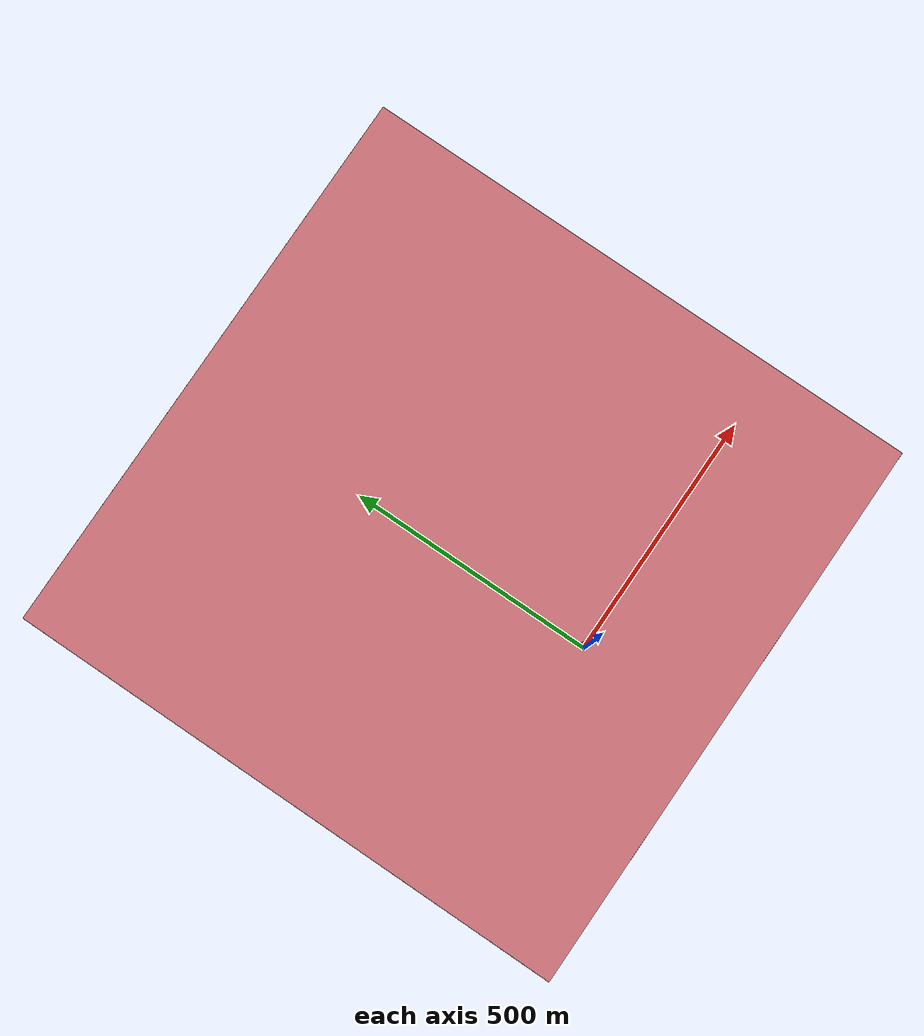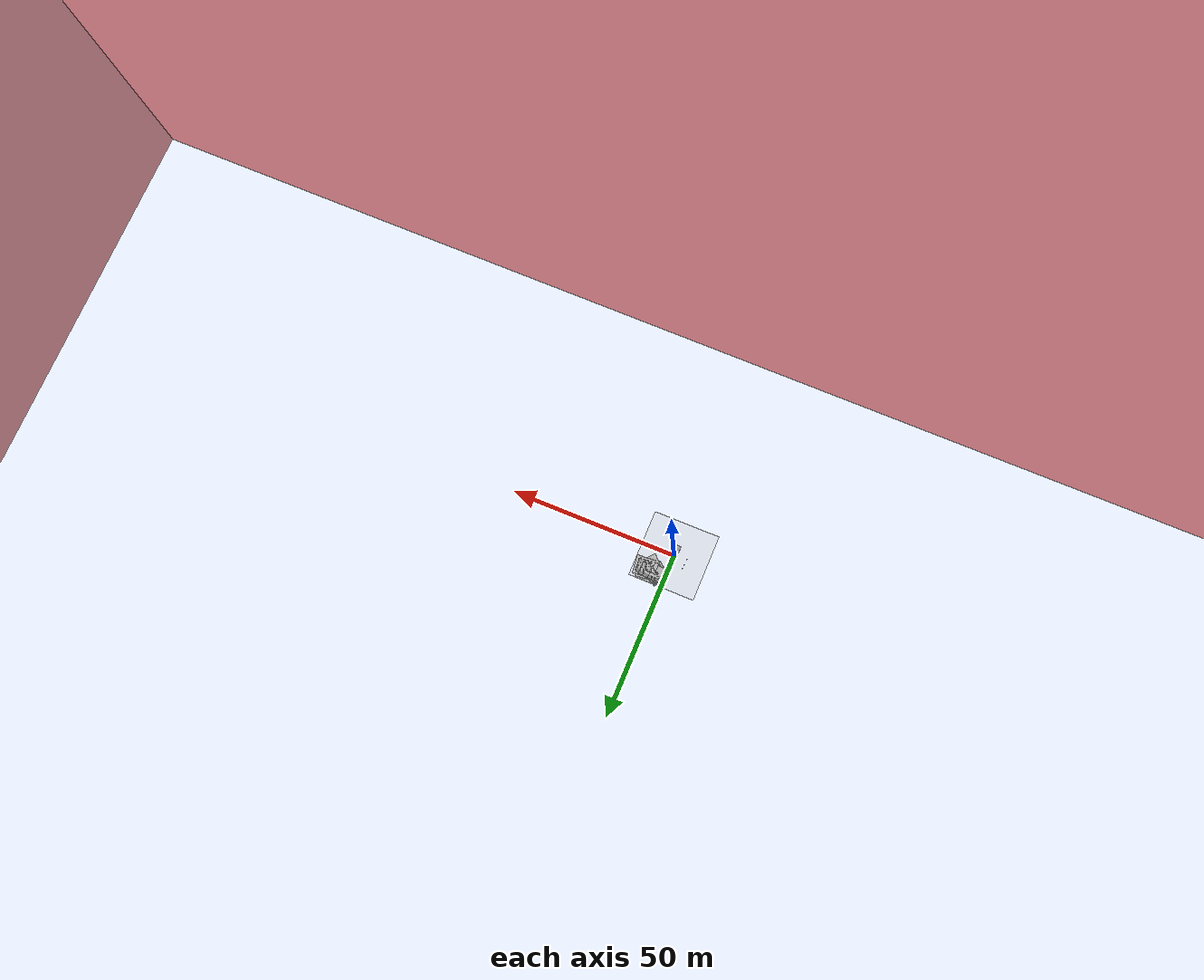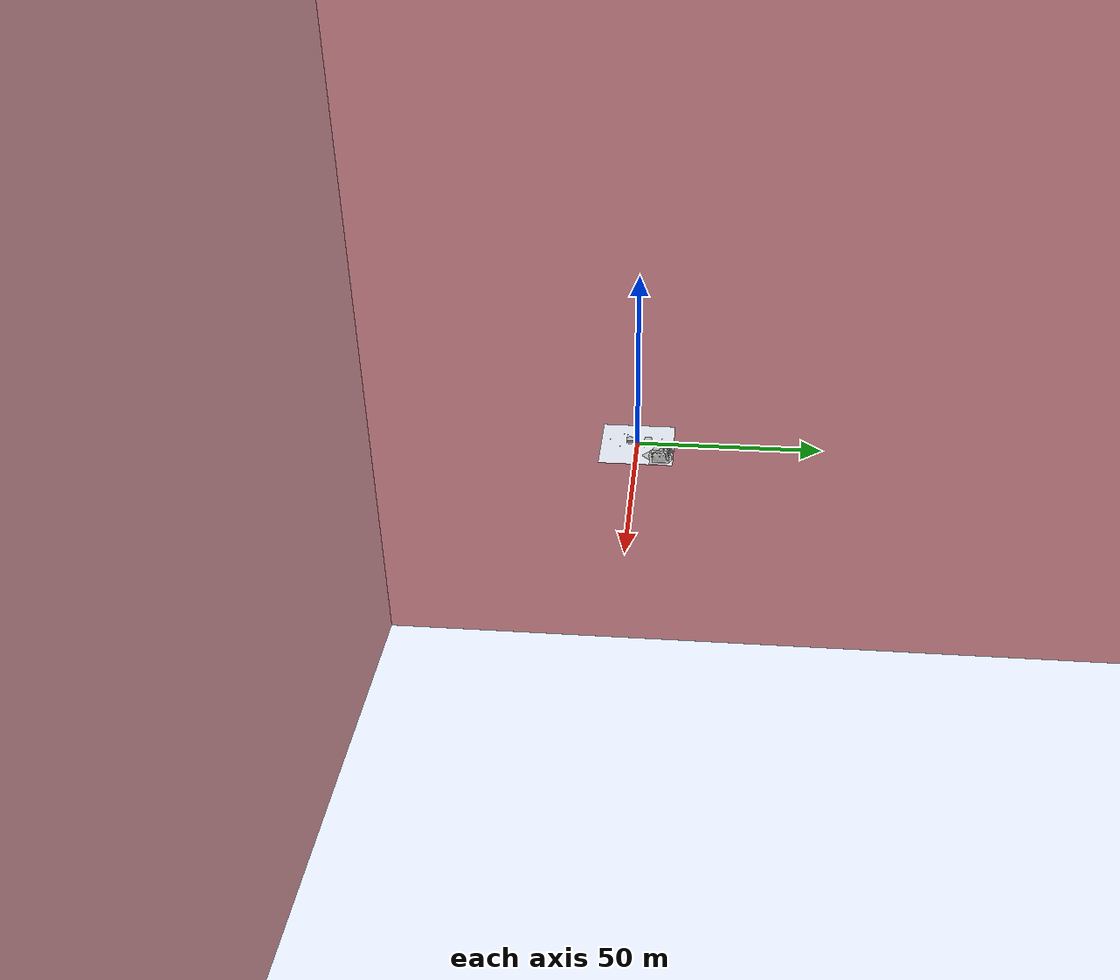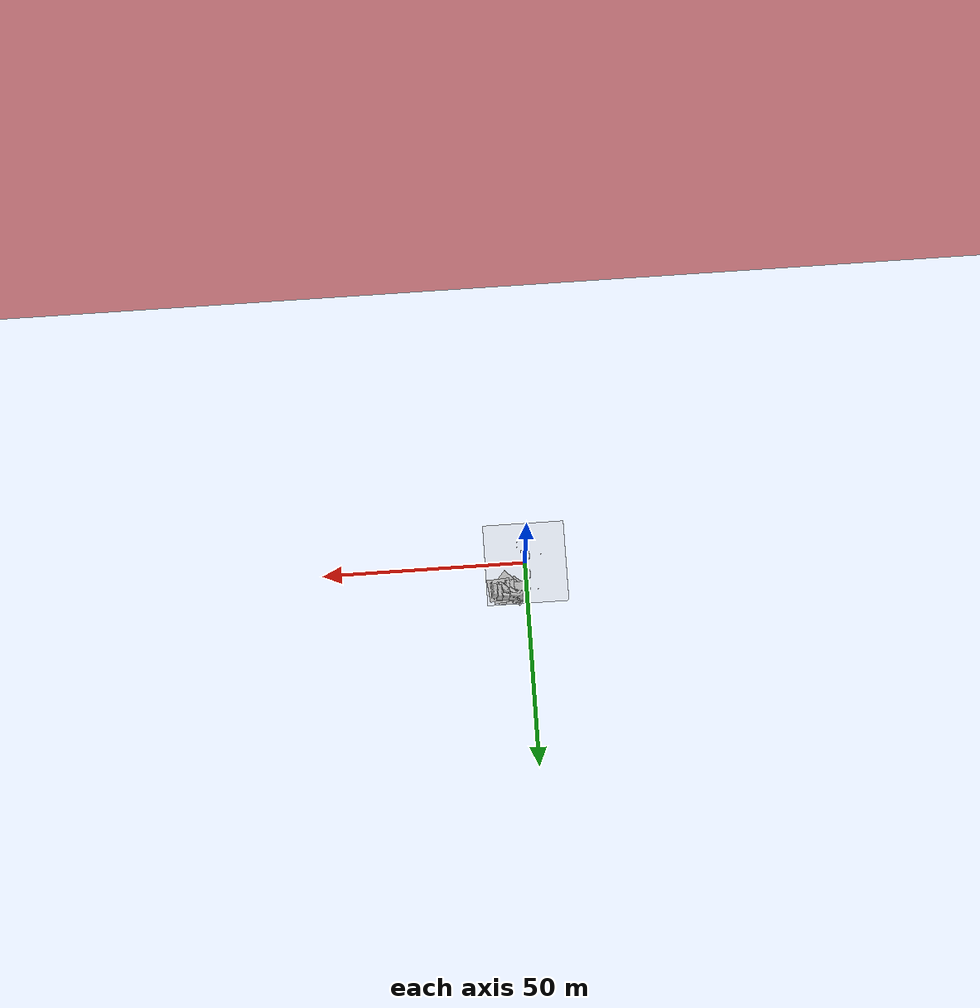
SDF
<sdf version="1.6">
 <world name="default">
  <light name="sun" type="directional">
   <pose>0 0 10 0 -0 0</pose>
   <diffuse>0.8 0.8 0.8 1</diffuse>
   <specular>0.1 0.1 0.1 1</specular>
   <attenuation>
    <range>1000</range>
    <constant>0.9</constant>
    <linear>0.01</linear>
    <quadratic>0.001</quadratic>
   </attenuation>
   <direction>-0.5 0.5 -1</direction>
  </light>
  <gravity>0 0 -9.8</gravity>
  <magnetic_field>6e-06 2.3e-05 -4.2e-05</magnetic_field>
  <atmosphere type="adiabatic"/>
  <physics name="default_physics" default="0" type="ode">
   <max_step_size>0.001</max_step_size>
   <real_time_factor>1</real_time_factor>
   <real_time_update_rate>1000</real_time_update_rate>
  </physics>
  <scene>
   <sky><clouds><speed>12</speed></clouds></sky>
   <ambient>0.4 0.4 0.4 1</ambient>
   <background>0.7 0.7 0.7 1</background>
   <shadows>1</shadows>
  </scene>
  <spherical_coordinates>
   <surface_model>EARTH_WGS84</surface_model>
   <latitude_deg>0</latitude_deg>
   <longitude_deg>0</longitude_deg>
   <elevation>0</elevation>
   <heading_deg>0</heading_deg>
  </spherical_coordinates>
  <model name="red_sky_filter">
   <link name="link_1">
    <visual name="visual1">
     <pose>-500 0 0 0 -0 1.5708</pose>
     <geometry><box><size>1000 0.1 1000</size></box></geometry>
     <material>
      <script><name>Gazebo/Red</name><uri>__default__</uri></script>
      <ambient>1 0 0 1</ambient>
      <diffuse>1 0 0 1</diffuse>
      <specular>1 0 0 1</specular>
      <emissive>1 0 0 1</emissive>
     </material>
     <transparency>0.4</transparency>
    </visual>
    <visual name="visual2">
     <pose>500 0 0 0 -0 1.5708</pose>
     <geometry><box><size>1000 0.1 1000</size></box></geometry>
     <material>
      <script><name>Gazebo/Red</name><uri>__default__</uri></script>
      <ambient>1 0 0 1</ambient>
      <diffuse>1 0 0 1</diffuse>
      <specular>1 0 0 1</specular>
      <emissive>1 0 0 1</emissive>
     </material>
     <transparency>0.4</transparency>
    </visual>
    <visual name="visual3">
     <pose>0 500 0 0 -0 0</pose>
     <geometry><box><size>1000 0.1 1000</size></box></geometry>
     <material>
      <script><name>Gazebo/Red</name><uri>__default__</uri></script>
      <ambient>1 0 0 1</ambient>
      <diffuse>1 0 0 1</diffuse>
      <specular>1 0 0 1</specular>
      <emissive>1 0 0 1</emissive>
     </material>
     <transparency>0.4</transparency>
    </visual>
    <visual name="visual4">
     <pose>0 -500 0 0 -0 0</pose>
     <geometry><box><size>1000 0.1 1000</size></box></geometry>
     <material>
      <script><name>Gazebo/Red</name><uri>__default__</uri></script>
      <ambient>1 0 0 1</ambient>
      <diffuse>1 0 0 1</diffuse>
      <specular>1 0 0 1</specular>
      <emissive>1 0 0 1</emissive>
     </material>
     <transparency>0.4</transparency>
    </visual>
    <visual name="visual5">
     <pose>0 0 500 0 -0 0</pose>
     <geometry><box><size>1000 1000 0.1</size></box></geometry>
     <material>
      <script><name>Gazebo/Red</name><uri>__default__</uri></script>
      <ambient>1 0 0 1</ambient>
      <diffuse>1 0 0 1</diffuse>
      <specular>1 0 0 1</specular>
      <emissive>1 0 0 1</emissive>
     </material>
     <transparency>0.4</transparency>
    </visual>
   </link>
   <static>1</static>
   <pose>3.85599 267.547 0 0 -0 0</pose>
  </model>
  <model name="collection_disk">
   <static>1</static>
   <link name="link">
    <visual name="visual">
     <geometry><box><size>1.016 1.016 0.001</size></box></geometry>
     <material>
      <script>
       <uri>model://collection_disk/materials/scripts</uri>
       <uri>model://collection_disk/materials/textures</uri>
       <name>collection_disk/Diffuse</name>
      </script>
     </material>
    </visual>
   </link>
   <plugin name="score_sim" filename="libgazebo_plugins_score.so">
    <scoreTopic>/collectionZone/score</scoreTopic>
    <collectionZoneSquareSize>1.016</collectionZoneSquareSize>
    <updateRate>0.2</updateRate>
   </plugin>
   <pose>0 3 0 0 -0 0</pose>
  </model>
  <model name="collection_disk_0">
   <static>1</static>
   <link name="link">
    <visual name="visual">
     <geometry><box><size>1.016 1.016 0.001</size></box></geometry>
     <material>
      <script>
       <uri>model://collection_disk/materials/scripts</uri>
       <uri>model://collection_disk/materials/textures</uri>
       <name>collection_disk/Diffuse</name>
      </script>
     </material>
    </visual>
   </link>
   <plugin name="score_sim" filename="libgazebo_plugins_score.so">
    <scoreTopic>/collectionZone/score</scoreTopic>
    <collectionZoneSquareSize>1.016</collectionZoneSquareSize>
    <updateRate>0.2</updateRate>
   </plugin>
   <pose>0 -2 0 0 -0 0</pose>
  </model>
  <model name="mission_to_mars_ground_plane_0">
   <static>1</static>
   <link name="link">
    <collision name="collision">
     <geometry><plane><normal>0 0 1</normal><size>20 20</size></plane></geometry>
     <surface><friction><ode><mu>100</mu><mu2>50</mu2></ode></friction></surface>
    </collision>
    <visual name="visual">
     <cast_shadows>0</cast_shadows>
     <geometry><plane><normal>0 0 1</normal><size>20 20</size></plane></geometry>
     <material>
      <script>
       <uri>model://media/materials/scripts</uri>
       <uri>model://media/materials/textures</uri>
       <name>MissionToMarsGround/Image</name>
      </script>
     </material>
    </visual>
   </link>
   <pose>-0.014064 -0.053068 0 0 -0 0</pose>
  </model>
  <model name="swarm_rock">
   <pose>2.9003 8.03828 -0.195688 3.14155 0.001592 1.54453</pose>
   <static>1</static>
   <link name="link">
    <collision name="collision">
     <geometry><mesh><uri>model://swarm_rock/meshes/swarm_rock.dae</uri><scale>1 1 1</scale></mesh></geometry>
    </collision>
    <visual name="visual">
     <geometry><mesh><uri>model://swarm_rock/meshes/swarm_rock.dae</uri><scale>1 1 1</scale></mesh></geometry>
    </visual>
   </link>
  </model>
  <model name="swarm_rock_0">
   <pose>3.3848 7.42046 -0.792328 3.14056 0.001213 0.865907</pose>
   <static>1</static>
   <link name="link">
    <collision name="collision">
     <geometry><mesh><uri>model://swarm_rock/meshes/swarm_rock.dae</uri><scale>1 1 1</scale></mesh></geometry>
    </collision>
    <visual name="visual">
     <geometry><mesh><uri>model://swarm_rock/meshes/swarm_rock.dae</uri><scale>1 1 1</scale></mesh></geometry>
    </visual>
   </link>
  </model>
  <model name="swarm_rock_1">
   <pose>5.82878 6.02298 -0.412309 3.1405 0.001156 0.811984</pose>
   <static>1</static>
   <link name="link">
    <collision name="collision">
     <geometry><mesh><uri>model://swarm_rock/meshes/swarm_rock.dae</uri><scale>1 1 1</scale></mesh></geometry>
    </collision>
    <visual name="visual">
     <geometry><mesh><uri>model://swarm_rock/meshes/swarm_rock.dae</uri><scale>1 1 1</scale></mesh></geometry>
    </visual>
   </link>
  </model>
  <model name="swarm_rock_2">
   <pose>7.92801 6.14651 0 3.14 -0 0</pose>
   <static>1</static>
   <link name="link">
    <collision name="collision">
     <geometry><mesh><uri>model://swarm_rock/meshes/swarm_rock.dae</uri><scale>1 1 1</scale></mesh></geometry>
    </collision>
    <visual name="visual">
     <geometry><mesh><uri>model://swarm_rock/meshes/swarm_rock.dae</uri><scale>1 1 1</scale></mesh></geometry>
    </visual>
   </link>
  </model>
  <model name="swarm_rock_3">
   <pose>4.64286 8.05527 -0.429706 3.14148 0.001589 1.5014</pose>
   <static>1</static>
   <link name="link">
    <collision name="collision">
     <geometry><mesh><uri>model://swarm_rock/meshes/swarm_rock.dae</uri><scale>1 1 1</scale></mesh></geometry>
    </collision>
    <visual name="visual">
     <geometry><mesh><uri>model://swarm_rock/meshes/swarm_rock.dae</uri><scale>1 1 1</scale></mesh></geometry>
    </visual>
   </link>
  </model>
  <model name="swarm_rock_4">
   <pose>6.83655 6.63858 0.001149 3.14 -0 0</pose>
   <static>1</static>
   <link name="link">
    <collision name="collision">
     <geometry><mesh><uri>model://swarm_rock/meshes/swarm_rock.dae</uri><scale>1 1 1</scale></mesh></geometry>
    </collision>
    <visual name="visual">
     <geometry><mesh><uri>model://swarm_rock/meshes/swarm_rock.dae</uri><scale>1 1 1</scale></mesh></geometry>
    </visual>
   </link>
  </model>
  <model name="tent">
   <pose>0.08978 2.87404 -0.451601 0 -0 0</pose>
   <static>1</static>
   <link name="link">
    <collision name="collision">
     <geometry><mesh><uri>model://tent/meshes/tent.dae</uri><scale>1 1 1</scale></mesh></geometry>
    </collision>
    <visual name="visual">
     <geometry><mesh><uri>model://tent/meshes/tent.dae</uri><scale>1 1 1</scale></mesh></geometry>
    </visual>
   </link>
  </model>
  <model name="tent_0">
   <pose>-0.009405 -1.98185 -0.567568 0 -0 0</pose>
   <static>1</static>
   <link name="link">
    <collision name="collision">
     <geometry><mesh><uri>model://tent/meshes/tent.dae</uri><scale>1 1 1</scale></mesh></geometry>
    </collision>
    <visual name="visual">
     <geometry><mesh><uri>model://tent/meshes/tent.dae</uri><scale>1 1 1</scale></mesh></geometry>
    </visual>
   </link>
  </model>
  <model name="at1">
   <static>0</static>
   <link name="link">
    <inertial>
     <mass>0.01</mass>
     <inertia><ixx>4e-05</ixx><ixy>0</ixy><ixz>0</ixz><iyy>4e-05</iyy><iyz>0</iyz><izz>4e-05</izz></inertia>
    </inertial>
    <visual name="visual">
     <geometry><box><size>0.05 0.05 0.05</size></box></geometry>
     <material>
      <script>
       <uri>model://at1/materials/scripts</uri>
       <uri>model://at1/materials/textures</uri>
       <name>at1/Diffuse</name>
      </script>
     </material>
    </visual>
    <collision name="collision">
     <geometry><box><size>0.05 0.05 0.05</size></box></geometry>
     <surface><friction><ode><mu>0.8</mu><mu2>0.7</mu2></ode></friction></surface>
    </collision>
   </link>
   <pose>-4.33918 -5.03118 0.025 0 -0 0</pose>
  </model>
  <model name="at1_1">
   <static>0</static>
   <link name="link">
    <inertial>
     <mass>0.01</mass>
     <inertia><ixx>4e-05</ixx><ixy>0</ixy><ixz>0</ixz><iyy>4e-05</iyy><iyz>0</iyz><izz>4e-05</izz></inertia>
    </inertial>
    <visual name="visual">
     <geometry><box><size>0.05 0.05 0.05</size></box></geometry>
     <material>
      <script>
       <uri>model://at1/materials/scripts</uri>
       <uri>model://at1/materials/textures</uri>
       <name>at1/Diffuse</name>
      </script>
     </material>
    </visual>
    <collision name="collision">
     <geometry><box><size>0.05 0.05 0.05</size></box></geometry>
     <surface><friction><ode><mu>0.8</mu><mu2>0.7</mu2></ode></friction></surface>
    </collision>
   </link>
   <pose>-4.39543 -4.71193 0.025 0 -0 0</pose>
  </model>
  <model name="at1_4">
   <static>0</static>
   <link name="link">
    <inertial>
     <mass>0.01</mass>
     <inertia><ixx>4e-05</ixx><ixy>0</ixy><ixz>0</ixz><iyy>4e-05</iyy><iyz>0</iyz><izz>4e-05</izz></inertia>
    </inertial>
    <visual name="visual">
     <geometry><box><size>0.05 0.05 0.05</size></box></geometry>
     <material>
      <script>
       <uri>model://at1/materials/scripts</uri>
       <uri>model://at1/materials/textures</uri>
       <name>at1/Diffuse</name>
      </script>
     </material>
    </visual>
    <collision name="collision">
     <geometry><box><size>0.05 0.05 0.05</size></box></geometry>
     <surface><friction><ode><mu>0.8</mu><mu2>0.7</mu2></ode></friction></surface>
    </collision>
   </link>
   <pose>-4.4502 -4.44028 0.025 0 -0 0</pose>
  </model>
  <model name="at1_7">
   <static>0</static>
   <link name="link">
    <inertial>
     <mass>0.01</mass>
     <inertia><ixx>4e-05</ixx><ixy>0</ixy><ixz>0</ixz><iyy>4e-05</iyy><iyz>0</iyz><izz>4e-05</izz></inertia>
    </inertial>
    <visual name="visual">
     <geometry><box><size>0.05 0.05 0.05</size></box></geometry>
     <material>
      <script>
       <uri>model://at1/materials/scripts</uri>
       <uri>model://at1/materials/textures</uri>
       <name>at1/Diffuse</name>
      </script>
     </material>
    </visual>
    <collision name="collision">
     <geometry><box><size>0.05 0.05 0.05</size></box></geometry>
     <surface><friction><ode><mu>0.8</mu><mu2>0.7</mu2></ode></friction></surface>
    </collision>
   </link>
   <pose>-4.52924 -4.17645 0.025 0 -0 0</pose>
  </model>
  <model name="at0">
   <static>0</static>
   <link name="link">
    <inertial>
     <mass>0.01</mass>
     <inertia><ixx>4e-05</ixx><ixy>0</ixy><ixz>0</ixz><iyy>4e-05</iyy><iyz>0</iyz><izz>4e-05</izz></inertia>
    </inertial>
    <visual name="visual">
     <geometry><box><size>0.05 0.05 0.05</size></box></geometry>
     <material>
      <script>
       <uri>model://at0/materials/scripts</uri>
       <uri>model://at0/materials/textures</uri>
       <name>at0/Diffuse</name>
      </script>
     </material>
    </visual>
    <collision name="collision">
     <geometry><box><size>0.05 0.05 0.05</size></box></geometry>
     <surface><friction><ode><mu>0.8</mu><mu2>0.7</mu2></ode></friction></surface>
    </collision>
   </link>
   <pose>-4.65444 -3.95452 0.025 0 -0 0</pose>
  </model>
  <model name="at1_8">
   <static>0</static>
   <link name="link">
    <inertial>
     <mass>0.01</mass>
     <inertia><ixx>4e-05</ixx><ixy>0</ixy><ixz>0</ixz><iyy>4e-05</iyy><iyz>0</iyz><izz>4e-05</izz></inertia>
    </inertial>
    <visual name="visual">
     <geometry><box><size>0.05 0.05 0.05</size></box></geometry>
     <material>
      <script>
       <uri>model://at1/materials/scripts</uri>
       <uri>model://at1/materials/textures</uri>
       <name>at1/Diffuse</name>
      </script>
     </material>
    </visual>
    <collision name="collision">
     <geometry><box><size>0.05 0.05 0.05</size></box></geometry>
     <surface><friction><ode><mu>0.8</mu><mu2>0.7</mu2></ode></friction></surface>
    </collision>
   </link>
   <pose>-4.35212 -3.76779 0.025 0 -0 0</pose>
  </model>
  <model name="at1_14">
   <static>0</static>
   <link name="link">
    <inertial>
     <mass>0.01</mass>
     <inertia><ixx>4e-05</ixx><ixy>0</ixy><ixz>0</ixz><iyy>4e-05</iyy><iyz>0</iyz><izz>4e-05</izz></inertia>
    </inertial>
    <visual name="visual">
     <geometry><box><size>0.05 0.05 0.05</size></box></geometry>
     <material>
      <script>
       <uri>model://at1/materials/scripts</uri>
       <uri>model://at1/materials/textures</uri>
       <name>at1/Diffuse</name>
      </script>
     </material>
    </visual>
    <collision name="collision">
     <geometry><box><size>0.05 0.05 0.05</size></box></geometry>
     <surface><friction><ode><mu>0.8</mu><mu2>0.7</mu2></ode></friction></surface>
    </collision>
   </link>
   <pose>-4.50515 -3.55361 0.025 0 -0 0</pose>
  </model>
  <model name="at1_15">
   <static>0</static>
   <link name="link">
    <inertial>
     <mass>0.01</mass>
     <inertia><ixx>4e-05</ixx><ixy>0</ixy><ixz>0</ixz><iyy>4e-05</iyy><iyz>0</iyz><izz>4e-05</izz></inertia>
    </inertial>
    <visual name="visual">
     <geometry><box><size>0.05 0.05 0.05</size></box></geometry>
     <material>
      <script>
       <uri>model://at1/materials/scripts</uri>
       <uri>model://at1/materials/textures</uri>
       <name>at1/Diffuse</name>
      </script>
     </material>
    </visual>
    <collision name="collision">
     <geometry><box><size>0.05 0.05 0.05</size></box></geometry>
     <surface><friction><ode><mu>0.8</mu><mu2>0.7</mu2></ode></friction></surface>
    </collision>
   </link>
   <pose>-4.21015 -3.27462 0.025 0 -0 0</pose>
  </model>
  <model name="at1_16">
   <static>0</static>
   <link name="link">
    <inertial>
     <mass>0.01</mass>
     <inertia><ixx>4e-05</ixx><ixy>0</ixy><ixz>0</ixz><iyy>4e-05</iyy><iyz>0</iyz><izz>4e-05</izz></inertia>
    </inertial>
    <visual name="visual">
     <geometry><box><size>0.05 0.05 0.05</size></box></geometry>
     <material>
      <script>
       <uri>model://at1/materials/scripts</uri>
       <uri>model://at1/materials/textures</uri>
       <name>at1/Diffuse</name>
      </script>
     </material>
    </visual>
    <collision name="collision">
     <geometry><box><size>0.05 0.05 0.05</size></box></geometry>
     <surface><friction><ode><mu>0.8</mu><mu2>0.7</mu2></ode></friction></surface>
    </collision>
   </link>
   <pose>-4.34331 -2.95495 0.025 0 -0 0</pose>
  </model>
  <model name="at1_17">
   <static>0</static>
   <link name="link">
    <inertial>
     <mass>0.01</mass>
     <inertia><ixx>4e-05</ixx><ixy>0</ixy><ixz>0</ixz><iyy>4e-05</iyy><iyz>0</iyz><izz>4e-05</izz></inertia>
    </inertial>
    <visual name="visual">
     <geometry><box><size>0.05 0.05 0.05</size></box></geometry>
     <material>
      <script>
       <uri>model://at1/materials/scripts</uri>
       <uri>model://at1/materials/textures</uri>
       <name>at1/Diffuse</name>
      </script>
     </material>
    </visual>
    <collision name="collision">
     <geometry><box><size>0.05 0.05 0.05</size></box></geometry>
     <surface><friction><ode><mu>0.8</mu><mu2>0.7</mu2></ode></friction></surface>
    </collision>
   </link>
   <pose>-4.1688 -2.76738 0.025 0 -0 0</pose>
  </model>
  <model name="at1_18">
   <static>0</static>
   <link name="link">
    <inertial>
     <mass>0.01</mass>
     <inertia><ixx>4e-05</ixx><ixy>0</ixy><ixz>0</ixz><iyy>4e-05</iyy><iyz>0</iyz><izz>4e-05</izz></inertia>
    </inertial>
    <visual name="visual">
     <geometry><box><size>0.05 0.05 0.05</size></box></geometry>
     <material>
      <script>
       <uri>model://at1/materials/scripts</uri>
       <uri>model://at1/materials/textures</uri>
       <name>at1/Diffuse</name>
      </script>
     </material>
    </visual>
    <collision name="collision">
     <geometry><box><size>0.05 0.05 0.05</size></box></geometry>
     <surface><friction><ode><mu>0.8</mu><mu2>0.7</mu2></ode></friction></surface>
    </collision>
   </link>
   <pose>-3.92643 -2.40079 0.025 0 -0 0</pose>
  </model>
  <model name="at1_19">
   <static>0</static>
   <link name="link">
    <inertial>
     <mass>0.01</mass>
     <inertia><ixx>4e-05</ixx><ixy>0</ixy><ixz>0</ixz><iyy>4e-05</iyy><iyz>0</iyz><izz>4e-05</izz></inertia>
    </inertial>
    <visual name="visual">
     <geometry><box><size>0.05 0.05 0.05</size></box></geometry>
     <material>
      <script>
       <uri>model://at1/materials/scripts</uri>
       <uri>model://at1/materials/textures</uri>
       <name>at1/Diffuse</name>
      </script>
     </material>
    </visual>
    <collision name="collision">
     <geometry><box><size>0.05 0.05 0.05</size></box></geometry>
     <surface><friction><ode><mu>0.8</mu><mu2>0.7</mu2></ode></friction></surface>
    </collision>
   </link>
   <pose>-4.16545 -2.29029 0.025 0 -0 0</pose>
  </model>
  <model name="at1_20">
   <static>0</static>
   <link name="link">
    <inertial>
     <mass>0.01</mass>
     <inertia><ixx>4e-05</ixx><ixy>0</ixy><ixz>0</ixz><iyy>4e-05</iyy><iyz>0</iyz><izz>4e-05</izz></inertia>
    </inertial>
    <visual name="visual">
     <geometry><box><size>0.05 0.05 0.05</size></box></geometry>
     <material>
      <script>
       <uri>model://at1/materials/scripts</uri>
       <uri>model://at1/materials/textures</uri>
       <name>at1/Diffuse</name>
      </script>
     </material>
    </visual>
    <collision name="collision">
     <geometry><box><size>0.05 0.05 0.05</size></box></geometry>
     <surface><friction><ode><mu>0.8</mu><mu2>0.7</mu2></ode></friction></surface>
    </collision>
   </link>
   <pose>-3.92061 -2.0184 0.025 0 -0 0</pose>
  </model>
  <model name="at1_21">
   <static>0</static>
   <link name="link">
    <inertial>
     <mass>0.01</mass>
     <inertia><ixx>4e-05</ixx><ixy>0</ixy><ixz>0</ixz><iyy>4e-05</iyy><iyz>0</iyz><izz>4e-05</izz></inertia>
    </inertial>
    <visual name="visual">
     <geometry><box><size>0.05 0.05 0.05</size></box></geometry>
     <material>
      <script>
       <uri>model://at1/materials/scripts</uri>
       <uri>model://at1/materials/textures</uri>
       <name>at1/Diffuse</name>
      </script>
     </material>
    </visual>
    <collision name="collision">
     <geometry><box><size>0.05 0.05 0.05</size></box></geometry>
     <surface><friction><ode><mu>0.8</mu><mu2>0.7</mu2></ode></friction></surface>
    </collision>
   </link>
   <pose>-3.85058 -1.4985 0.025 0 -0 0</pose>
  </model>
  <model name="at1_22">
   <static>0</static>
   <link name="link">
    <inertial>
     <mass>0.01</mass>
     <inertia><ixx>4e-05</ixx><ixy>0</ixy><ixz>0</ixz><iyy>4e-05</iyy><iyz>0</iyz><izz>4e-05</izz></inertia>
    </inertial>
    <visual name="visual">
     <geometry><box><size>0.05 0.05 0.05</size></box></geometry>
     <material>
      <script>
       <uri>model://at1/materials/scripts</uri>
       <uri>model://at1/materials/textures</uri>
       <name>at1/Diffuse</name>
      </script>
     </material>
    </visual>
    <collision name="collision">
     <geometry><box><size>0.05 0.05 0.05</size></box></geometry>
     <surface><friction><ode><mu>0.8</mu><mu2>0.7</mu2></ode></friction></surface>
    </collision>
   </link>
   <pose>-4.03776 -1.63458 0.025 0 -0 0</pose>
  </model>
  <model name="at1_23">
   <static>0</static>
   <link name="link">
    <inertial>
     <mass>0.01</mass>
     <inertia><ixx>4e-05</ixx><ixy>0</ixy><ixz>0</ixz><iyy>4e-05</iyy><iyz>0</iyz><izz>4e-05</izz></inertia>
    </inertial>
    <visual name="visual">
     <geometry><box><size>0.05 0.05 0.05</size></box></geometry>
     <material>
      <script>
       <uri>model://at1/materials/scripts</uri>
       <uri>model://at1/materials/textures</uri>
       <name>at1/Diffuse</name>
      </script>
     </material>
    </visual>
    <collision name="collision">
     <geometry><box><size>0.05 0.05 0.05</size></box></geometry>
     <surface><friction><ode><mu>0.8</mu><mu2>0.7</mu2></ode></friction></surface>
    </collision>
   </link>
   <pose>-3.81272 -0.749757 0.025 0 -0 0</pose>
  </model>
  <model name="at1_24">
   <static>0</static>
   <link name="link">
    <inertial>
     <mass>0.01</mass>
     <inertia><ixx>4e-05</ixx><ixy>0</ixy><ixz>0</ixz><iyy>4e-05</iyy><iyz>0</iyz><izz>4e-05</izz></inertia>
    </inertial>
    <visual name="visual">
     <geometry><box><size>0.05 0.05 0.05</size></box></geometry>
     <material>
      <script>
       <uri>model://at1/materials/scripts</uri>
       <uri>model://at1/materials/textures</uri>
       <name>at1/Diffuse</name>
      </script>
     </material>
    </visual>
    <collision name="collision">
     <geometry><box><size>0.05 0.05 0.05</size></box></geometry>
     <surface><friction><ode><mu>0.8</mu><mu2>0.7</mu2></ode></friction></surface>
    </collision>
   </link>
   <pose>-3.91632 -0.311172 0.025 0 -0 0</pose>
  </model>
  <model name="at1_25">
   <static>0</static>
   <link name="link">
    <inertial>
     <mass>0.01</mass>
     <inertia><ixx>4e-05</ixx><ixy>0</ixy><ixz>0</ixz><iyy>4e-05</iyy><iyz>0</iyz><izz>4e-05</izz></inertia>
    </inertial>
    <visual name="visual">
     <geometry><box><size>0.05 0.05 0.05</size></box></geometry>
     <material>
      <script>
       <uri>model://at1/materials/scripts</uri>
       <uri>model://at1/materials/textures</uri>
       <name>at1/Diffuse</name>
      </script>
     </material>
    </visual>
    <collision name="collision">
     <geometry><box><size>0.05 0.05 0.05</size></box></geometry>
     <surface><friction><ode><mu>0.8</mu><mu2>0.7</mu2></ode></friction></surface>
    </collision>
   </link>
   <pose>-3.86256 0.145044 0.025 0 -0 0</pose>
  </model>
  <model name="at1_26">
   <static>0</static>
   <link name="link">
    <inertial>
     <mass>0.01</mass>
     <inertia><ixx>4e-05</ixx><ixy>0</ixy><ixz>0</ixz><iyy>4e-05</iyy><iyz>0</iyz><izz>4e-05</izz></inertia>
    </inertial>
    <visual name="visual">
     <geometry><box><size>0.05 0.05 0.05</size></box></geometry>
     <material>
      <script>
       <uri>model://at1/materials/scripts</uri>
       <uri>model://at1/materials/textures</uri>
       <name>at1/Diffuse</name>
      </script>
     </material>
    </visual>
    <collision name="collision">
     <geometry><box><size>0.05 0.05 0.05</size></box></geometry>
     <surface><friction><ode><mu>0.8</mu><mu2>0.7</mu2></ode></friction></surface>
    </collision>
   </link>
   <pose>-3.81393 0.692017 0.025 0 -0 0</pose>
  </model>
  <model name="at1_27">
   <static>0</static>
   <link name="link">
    <inertial>
     <mass>0.01</mass>
     <inertia><ixx>4e-05</ixx><ixy>0</ixy><ixz>0</ixz><iyy>4e-05</iyy><iyz>0</iyz><izz>4e-05</izz></inertia>
    </inertial>
    <visual name="visual">
     <geometry><box><size>0.05 0.05 0.05</size></box></geometry>
     <material>
      <script>
       <uri>model://at1/materials/scripts</uri>
       <uri>model://at1/materials/textures</uri>
       <name>at1/Diffuse</name>
      </script>
     </material>
    </visual>
    <collision name="collision">
     <geometry><box><size>0.05 0.05 0.05</size></box></geometry>
     <surface><friction><ode><mu>0.8</mu><mu2>0.7</mu2></ode></friction></surface>
    </collision>
   </link>
   <pose>-3.90149 0.941367 0.025 0 -0 0</pose>
  </model>
  <model name="at1_28">
   <static>0</static>
   <link name="link">
    <inertial>
     <mass>0.01</mass>
     <inertia><ixx>4e-05</ixx><ixy>0</ixy><ixz>0</ixz><iyy>4e-05</iyy><iyz>0</iyz><izz>4e-05</izz></inertia>
    </inertial>
    <visual name="visual">
     <geometry><box><size>0.05 0.05 0.05</size></box></geometry>
     <material>
      <script>
       <uri>model://at1/materials/scripts</uri>
       <uri>model://at1/materials/textures</uri>
       <name>at1/Diffuse</name>
      </script>
     </material>
    </visual>
    <collision name="collision">
     <geometry><box><size>0.05 0.05 0.05</size></box></geometry>
     <surface><friction><ode><mu>0.8</mu><mu2>0.7</mu2></ode></friction></surface>
    </collision>
   </link>
   <pose>-3.7815 1.42667 0.025 0 -0 0</pose>
  </model>
  <model name="at1_29">
   <static>0</static>
   <link name="link">
    <inertial>
     <mass>0.01</mass>
     <inertia><ixx>4e-05</ixx><ixy>0</ixy><ixz>0</ixz><iyy>4e-05</iyy><iyz>0</iyz><izz>4e-05</izz></inertia>
    </inertial>
    <visual name="visual">
     <geometry><box><size>0.05 0.05 0.05</size></box></geometry>
     <material>
      <script>
       <uri>model://at1/materials/scripts</uri>
       <uri>model://at1/materials/textures</uri>
       <name>at1/Diffuse</name>
      </script>
     </material>
    </visual>
    <collision name="collision">
     <geometry><box><size>0.05 0.05 0.05</size></box></geometry>
     <surface><friction><ode><mu>0.8</mu><mu2>0.7</mu2></ode></friction></surface>
    </collision>
   </link>
   <pose>-3.76028 1.98357 0.025 0 -0 0</pose>
  </model>
  <model name="at1_30">
   <static>0</static>
   <link name="link">
    <inertial>
     <mass>0.01</mass>
     <inertia><ixx>4e-05</ixx><ixy>0</ixy><ixz>0</ixz><iyy>4e-05</iyy><iyz>0</iyz><izz>4e-05</izz></inertia>
    </inertial>
    <visual name="visual">
     <geometry><box><size>0.05 0.05 0.05</size></box></geometry>
     <material>
      <script>
       <uri>model://at1/materials/scripts</uri>
       <uri>model://at1/materials/textures</uri>
       <name>at1/Diffuse</name>
      </script>
     </material>
    </visual>
    <collision name="collision">
     <geometry><box><size>0.05 0.05 0.05</size></box></geometry>
     <surface><friction><ode><mu>0.8</mu><mu2>0.7</mu2></ode></friction></surface>
    </collision>
   </link>
   <pose>-3.73691 2.59768 0.025 0 -0 0</pose>
  </model>
  <model name="at0_0">
   <static>0</static>
   <link name="link">
    <inertial>
     <mass>0.01</mass>
     <inertia><ixx>4e-05</ixx><ixy>0</ixy><ixz>0</ixz><iyy>4e-05</iyy><iyz>0</iyz><izz>4e-05</izz></inertia>
    </inertial>
    <visual name="visual">
     <geometry><box><size>0.05 0.05 0.05</size></box></geometry>
     <material>
      <script>
       <uri>model://at0/materials/scripts</uri>
       <uri>model://at0/materials/textures</uri>
       <name>at0/Diffuse</name>
      </script>
     </material>
    </visual>
    <collision name="collision">
     <geometry><box><size>0.05 0.05 0.05</size></box></geometry>
     <surface><friction><ode><mu>0.8</mu><mu2>0.7</mu2></ode></friction></surface>
    </collision>
   </link>
   <pose>-3.46326 2.95949 0.025 0 -0 0</pose>
  </model>
  <model name="at1_31">
   <static>0</static>
   <link name="link">
    <inertial>
     <mass>0.01</mass>
     <inertia><ixx>4e-05</ixx><ixy>0</ixy><ixz>0</ixz><iyy>4e-05</iyy><iyz>0</iyz><izz>4e-05</izz></inertia>
    </inertial>
    <visual name="visual">
     <geometry><box><size>0.05 0.05 0.05</size></box></geometry>
     <material>
      <script>
       <uri>model://at1/materials/scripts</uri>
       <uri>model://at1/materials/textures</uri>
       <name>at1/Diffuse</name>
      </script>
     </material>
    </visual>
    <collision name="collision">
     <geometry><box><size>0.05 0.05 0.05</size></box></geometry>
     <surface><friction><ode><mu>0.8</mu><mu2>0.7</mu2></ode></friction></surface>
    </collision>
   </link>
   <pose>-3.71224 3.0632 0.025 0 -0 0</pose>
  </model>
  <model name="at1_32">
   <static>0</static>
   <link name="link">
    <inertial>
     <mass>0.01</mass>
     <inertia><ixx>4e-05</ixx><ixy>0</ixy><ixz>0</ixz><iyy>4e-05</iyy><iyz>0</iyz><izz>4e-05</izz></inertia>
    </inertial>
    <visual name="visual">
     <geometry><box><size>0.05 0.05 0.05</size></box></geometry>
     <material>
      <script>
       <uri>model://at1/materials/scripts</uri>
       <uri>model://at1/materials/textures</uri>
       <name>at1/Diffuse</name>
      </script>
     </material>
    </visual>
    <collision name="collision">
     <geometry><box><size>0.05 0.05 0.05</size></box></geometry>
     <surface><friction><ode><mu>0.8</mu><mu2>0.7</mu2></ode></friction></surface>
    </collision>
   </link>
   <pose>-3.197 3.56075 0.025 0 -0 0</pose>
  </model>
  <model name="at1_33">
   <static>0</static>
   <link name="link">
    <inertial>
     <mass>0.01</mass>
     <inertia><ixx>4e-05</ixx><ixy>0</ixy><ixz>0</ixz><iyy>4e-05</iyy><iyz>0</iyz><izz>4e-05</izz></inertia>
    </inertial>
    <visual name="visual">
     <geometry><box><size>0.05 0.05 0.05</size></box></geometry>
     <material>
      <script>
       <uri>model://at1/materials/scripts</uri>
       <uri>model://at1/materials/textures</uri>
       <name>at1/Diffuse</name>
      </script>
     </material>
    </visual>
    <collision name="collision">
     <geometry><box><size>0.05 0.05 0.05</size></box></geometry>
     <surface><friction><ode><mu>0.8</mu><mu2>0.7</mu2></ode></friction></surface>
    </collision>
   </link>
   <pose>-3.43692 3.6011 0.025 0 -0 0</pose>
  </model>
  <model name="at1_34">
   <static>0</static>
   <link name="link">
    <inertial>
     <mass>0.01</mass>
     <inertia><ixx>4e-05</ixx><ixy>0</ixy><ixz>0</ixz><iyy>4e-05</iyy><iyz>0</iyz><izz>4e-05</izz></inertia>
    </inertial>
    <visual name="visual">
     <geometry><box><size>0.05 0.05 0.05</size></box></geometry>
     <material>
      <script>
       <uri>model://at1/materials/scripts</uri>
       <uri>model://at1/materials/textures</uri>
       <name>at1/Diffuse</name>
      </script>
     </material>
    </visual>
    <collision name="collision">
     <geometry><box><size>0.05 0.05 0.05</size></box></geometry>
     <surface><friction><ode><mu>0.8</mu><mu2>0.7</mu2></ode></friction></surface>
    </collision>
   </link>
   <pose>-3.30602 4.01729 0.025 0 -0 0</pose>
  </model>
  <model name="at1_35">
   <static>0</static>
   <link name="link">
    <inertial>
     <mass>0.01</mass>
     <inertia><ixx>4e-05</ixx><ixy>0</ixy><ixz>0</ixz><iyy>4e-05</iyy><iyz>0</iyz><izz>4e-05</izz></inertia>
    </inertial>
    <visual name="visual">
     <geometry><box><size>0.05 0.05 0.05</size></box></geometry>
     <material>
      <script>
       <uri>model://at1/materials/scripts</uri>
       <uri>model://at1/materials/textures</uri>
       <name>at1/Diffuse</name>
      </script>
     </material>
    </visual>
    <collision name="collision">
     <geometry><box><size>0.05 0.05 0.05</size></box></geometry>
     <surface><friction><ode><mu>0.8</mu><mu2>0.7</mu2></ode></friction></surface>
    </collision>
   </link>
   <pose>-3.21362 4.39236 0.025 0 -0 0</pose>
  </model>
  <model name="at1_36">
   <static>0</static>
   <link name="link">
    <inertial>
     <mass>0.01</mass>
     <inertia><ixx>4e-05</ixx><ixy>0</ixy><ixz>0</ixz><iyy>4e-05</iyy><iyz>0</iyz><izz>4e-05</izz></inertia>
    </inertial>
    <visual name="visual">
     <geometry><box><size>0.05 0.05 0.05</size></box></geometry>
     <material>
      <script>
       <uri>model://at1/materials/scripts</uri>
       <uri>model://at1/materials/textures</uri>
       <name>at1/Diffuse</name>
      </script>
     </material>
    </visual>
    <collision name="collision">
     <geometry><box><size>0.05 0.05 0.05</size></box></geometry>
     <surface><friction><ode><mu>0.8</mu><mu2>0.7</mu2></ode></friction></surface>
    </collision>
   </link>
   <pose>-3.3271 4.38736 0.025 0 -0 0</pose>
  </model>
  <model name="at1_37">
   <static>0</static>
   <link name="link">
    <inertial>
     <mass>0.01</mass>
     <inertia><ixx>4e-05</ixx><ixy>0</ixy><ixz>0</ixz><iyy>4e-05</iyy><iyz>0</iyz><izz>4e-05</izz></inertia>
    </inertial>
    <visual name="visual">
     <geometry><box><size>0.05 0.05 0.05</size></box></geometry>
     <material>
      <script>
       <uri>model://at1/materials/scripts</uri>
       <uri>model://at1/materials/textures</uri>
       <name>at1/Diffuse</name>
      </script>
     </material>
    </visual>
    <collision name="collision">
     <geometry><box><size>0.05 0.05 0.05</size></box></geometry>
     <surface><friction><ode><mu>0.8</mu><mu2>0.7</mu2></ode></friction></surface>
    </collision>
   </link>
   <pose>-3.1886 4.66437 0.025 0 -0 0</pose>
  </model>
  <model name="at1_38">
   <static>0</static>
   <link name="link">
    <inertial>
     <mass>0.01</mass>
     <inertia><ixx>4e-05</ixx><ixy>0</ixy><ixz>0</ixz><iyy>4e-05</iyy><iyz>0</iyz><izz>4e-05</izz></inertia>
    </inertial>
    <visual name="visual">
     <geometry><box><size>0.05 0.05 0.05</size></box></geometry>
     <material>
      <script>
       <uri>model://at1/materials/scripts</uri>
       <uri>model://at1/materials/textures</uri>
       <name>at1/Diffuse</name>
      </script>
     </material>
    </visual>
    <collision name="collision">
     <geometry><box><size>0.05 0.05 0.05</size></box></geometry>
     <surface><friction><ode><mu>0.8</mu><mu2>0.7</mu2></ode></friction></surface>
    </collision>
   </link>
   <pose>-3.30325 4.96735 0.025 0 -0 0</pose>
  </model>
  <model name="at1_39">
   <static>0</static>
   <link name="link">
    <inertial>
     <mass>0.01</mass>
     <inertia><ixx>4e-05</ixx><ixy>0</ixy><ixz>0</ixz><iyy>4e-05</iyy><iyz>0</iyz><izz>4e-05</izz></inertia>
    </inertial>
    <visual name="visual">
     <geometry><box><size>0.05 0.05 0.05</size></box></geometry>
     <material>
      <script>
       <uri>model://at1/materials/scripts</uri>
       <uri>model://at1/materials/textures</uri>
       <name>at1/Diffuse</name>
      </script>
     </material>
    </visual>
    <collision name="collision">
     <geometry><box><size>0.05 0.05 0.05</size></box></geometry>
     <surface><friction><ode><mu>0.8</mu><mu2>0.7</mu2></ode></friction></surface>
    </collision>
   </link>
   <pose>-3.09371 5.10767 0.025 0 -0 0</pose>
  </model>
  <model name="at1_40">
   <static>0</static>
   <link name="link">
    <inertial>
     <mass>0.01</mass>
     <inertia><ixx>4e-05</ixx><ixy>0</ixy><ixz>0</ixz><iyy>4e-05</iyy><iyz>0</iyz><izz>4e-05</izz></inertia>
    </inertial>
    <visual name="visual">
     <geometry><box><size>0.05 0.05 0.05</size></box></geometry>
     <material>
      <script>
       <uri>model://at1/materials/scripts</uri>
       <uri>model://at1/materials/textures</uri>
       <name>at1/Diffuse</name>
      </script>
     </material>
    </visual>
    <collision name="collision">
     <geometry><box><size>0.05 0.05 0.05</size></box></geometry>
     <surface><friction><ode><mu>0.8</mu><mu2>0.7</mu2></ode></friction></surface>
    </collision>
   </link>
   <pose>-3.0999 5.49958 0.025 0 -0 0</pose>
  </model>
  <model name="at1_41">
   <static>0</static>
   <link name="link">
    <inertial>
     <mass>0.01</mass>
     <inertia><ixx>4e-05</ixx><ixy>0</ixy><ixz>0</ixz><iyy>4e-05</iyy><iyz>0</iyz><izz>4e-05</izz></inertia>
    </inertial>
    <visual name="visual">
     <geometry><box><size>0.05 0.05 0.05</size></box></geometry>
     <material>
      <script>
       <uri>model://at1/materials/scripts</uri>
       <uri>model://at1/materials/textures</uri>
       <name>at1/Diffuse</name>
      </script>
     </material>
    </visual>
    <collision name="collision">
     <geometry><box><size>0.05 0.05 0.05</size></box></geometry>
     <surface><friction><ode><mu>0.8</mu><mu2>0.7</mu2></ode></friction></surface>
    </collision>
   </link>
   <pose>-3.09403 5.8738 0.025 0 -0 0</pose>
  </model>
  <model name="at1_42">
   <static>0</static>
   <link name="link">
    <inertial>
     <mass>0.01</mass>
     <inertia><ixx>4e-05</ixx><ixy>0</ixy><ixz>0</ixz><iyy>4e-05</iyy><iyz>0</iyz><izz>4e-05</izz></inertia>
    </inertial>
    <visual name="visual">
     <geometry><box><size>0.05 0.05 0.05</size></box></geometry>
     <material>
      <script>
       <uri>model://at1/materials/scripts</uri>
       <uri>model://at1/materials/textures</uri>
       <name>at1/Diffuse</name>
      </script>
     </material>
    </visual>
    <collision name="collision">
     <geometry><box><size>0.05 0.05 0.05</size></box></geometry>
     <surface><friction><ode><mu>0.8</mu><mu2>0.7</mu2></ode></friction></surface>
    </collision>
   </link>
   <pose>-2.97522 6.15874 0.025 0 -0 0</pose>
  </model>
  <model name="at1_43">
   <static>0</static>
   <link name="link">
    <inertial>
     <mass>0.01</mass>
     <inertia><ixx>4e-05</ixx><ixy>0</ixy><ixz>0</ixz><iyy>4e-05</iyy><iyz>0</iyz><izz>4e-05</izz></inertia>
    </inertial>
    <visual name="visual">
     <geometry><box><size>0.05 0.05 0.05</size></box></geometry>
     <material>
      <script>
       <uri>model://at1/materials/scripts</uri>
       <uri>model://at1/materials/textures</uri>
       <name>at1/Diffuse</name>
      </script>
     </material>
    </visual>
    <collision name="collision">
     <geometry><box><size>0.05 0.05 0.05</size></box></geometry>
     <surface><friction><ode><mu>0.8</mu><mu2>0.7</mu2></ode></friction></surface>
    </collision>
   </link>
   <pose>-2.91865 6.50611 0.025 0 -0 0</pose>
  </model>
  <model name="at1_44">
   <static>0</static>
   <link name="link">
    <inertial>
     <mass>0.01</mass>
     <inertia><ixx>4e-05</ixx><ixy>0</ixy><ixz>0</ixz><iyy>4e-05</iyy><iyz>0</iyz><izz>4e-05</izz></inertia>
    </inertial>
    <visual name="visual">
     <geometry><box><size>0.05 0.05 0.05</size></box></geometry>
     <material>
      <script>
       <uri>model://at1/materials/scripts</uri>
       <uri>model://at1/materials/textures</uri>
       <name>at1/Diffuse</name>
      </script>
     </material>
    </visual>
    <collision name="collision">
     <geometry><box><size>0.05 0.05 0.05</size></box></geometry>
     <surface><friction><ode><mu>0.8</mu><mu2>0.7</mu2></ode></friction></surface>
    </collision>
   </link>
   <pose>-2.73617 6.62491 0.025 0 -0 0</pose>
  </model>
  <model name="at0_1">
   <static>0</static>
   <link name="link">
    <inertial>
     <mass>0.01</mass>
     <inertia><ixx>4e-05</ixx><ixy>0</ixy><ixz>0</ixz><iyy>4e-05</iyy><iyz>0</iyz><izz>4e-05</izz></inertia>
    </inertial>
    <visual name="visual">
     <geometry><box><size>0.05 0.05 0.05</size></box></geometry>
     <material>
      <script>
       <uri>model://at0/materials/scripts</uri>
       <uri>model://at0/materials/textures</uri>
       <name>at0/Diffuse</name>
      </script>
     </material>
    </visual>
    <collision name="collision">
     <geometry><box><size>0.05 0.05 0.05</size></box></geometry>
     <surface><friction><ode><mu>0.8</mu><mu2>0.7</mu2></ode></friction></surface>
    </collision>
   </link>
   <pose>2.90292 -5.01991 0.025 0 -0 0</pose>
  </model>
  <model name="at0_2">
   <static>0</static>
   <link name="link">
    <inertial>
     <mass>0.01</mass>
     <inertia><ixx>4e-05</ixx><ixy>0</ixy><ixz>0</ixz><iyy>4e-05</iyy><iyz>0</iyz><izz>4e-05</izz></inertia>
    </inertial>
    <visual name="visual">
     <geometry><box><size>0.05 0.05 0.05</size></box></geometry>
     <material>
      <script>
       <uri>model://at0/materials/scripts</uri>
       <uri>model://at0/materials/textures</uri>
       <name>at0/Diffuse</name>
      </script>
     </material>
    </visual>
    <collision name="collision">
     <geometry><box><size>0.05 0.05 0.05</size></box></geometry>
     <surface><friction><ode><mu>0.8</mu><mu2>0.7</mu2></ode></friction></surface>
    </collision>
   </link>
   <pose>2.67435 -5.21124 0.025 0 -0 0</pose>
  </model>
  <model name="at0_3">
   <static>0</static>
   <link name="link">
    <inertial>
     <mass>0.01</mass>
     <inertia><ixx>4e-05</ixx><ixy>0</ixy><ixz>0</ixz><iyy>4e-05</iyy><iyz>0</iyz><izz>4e-05</izz></inertia>
    </inertial>
    <visual name="visual">
     <geometry><box><size>0.05 0.05 0.05</size></box></geometry>
     <material>
      <script>
       <uri>model://at0/materials/scripts</uri>
       <uri>model://at0/materials/textures</uri>
       <name>at0/Diffuse</name>
      </script>
     </material>
    </visual>
    <collision name="collision">
     <geometry><box><size>0.05 0.05 0.05</size></box></geometry>
     <surface><friction><ode><mu>0.8</mu><mu2>0.7</mu2></ode></friction></surface>
    </collision>
   </link>
   <pose>2.90118 -4.53855 0.025 0 -0 0</pose>
  </model>
  <model name="at0_4">
   <static>0</static>
   <link name="link">
    <inertial>
     <mass>0.01</mass>
     <inertia><ixx>4e-05</ixx><ixy>0</ixy><ixz>0</ixz><iyy>4e-05</iyy><iyz>0</iyz><izz>4e-05</izz></inertia>
    </inertial>
    <visual name="visual">
     <geometry><box><size>0.05 0.05 0.05</size></box></geometry>
     <material>
      <script>
       <uri>model://at0/materials/scripts</uri>
       <uri>model://at0/materials/textures</uri>
       <name>at0/Diffuse</name>
      </script>
     </material>
    </visual>
    <collision name="collision">
     <geometry><box><size>0.05 0.05 0.05</size></box></geometry>
     <surface><friction><ode><mu>0.8</mu><mu2>0.7</mu2></ode></friction></surface>
    </collision>
   </link>
   <pose>2.6418 -4.86366 0.025 0 -0 0</pose>
  </model>
  <model name="at0_5">
   <static>0</static>
   <link name="link">
    <inertial>
     <mass>0.01</mass>
     <inertia><ixx>4e-05</ixx><ixy>0</ixy><ixz>0</ixz><iyy>4e-05</iyy><iyz>0</iyz><izz>4e-05</izz></inertia>
    </inertial>
    <visual name="visual">
     <geometry><box><size>0.05 0.05 0.05</size></box></geometry>
     <material>
      <script>
       <uri>model://at0/materials/scripts</uri>
       <uri>model://at0/materials/textures</uri>
       <name>at0/Diffuse</name>
      </script>
     </material>
    </visual>
    <collision name="collision">
     <geometry><box><size>0.05 0.05 0.05</size></box></geometry>
     <surface><friction><ode><mu>0.8</mu><mu2>0.7</mu2></ode></friction></surface>
    </collision>
   </link>
   <pose>2.11687 -5.18129 0.025 0 -0 0</pose>
  </model>
  <model name="at0_6">
   <static>0</static>
   <link name="link">
    <inertial>
     <mass>0.01</mass>
     <inertia><ixx>4e-05</ixx><ixy>0</ixy><ixz>0</ixz><iyy>4e-05</iyy><iyz>0</iyz><izz>4e-05</izz></inertia>
    </inertial>
    <visual name="visual">
     <geometry><box><size>0.05 0.05 0.05</size></box></geometry>
     <material>
      <script>
       <uri>model://at0/materials/scripts</uri>
       <uri>model://at0/materials/textures</uri>
       <name>at0/Diffuse</name>
      </script>
     </material>
    </visual>
    <collision name="collision">
     <geometry><box><size>0.05 0.05 0.05</size></box></geometry>
     <surface><friction><ode><mu>0.8</mu><mu2>0.7</mu2></ode></friction></surface>
    </collision>
   </link>
   <pose>2.8308 -3.97412 0.025 0 -0 0</pose>
  </model>
  <model name="at0_7">
   <static>0</static>
   <link name="link">
    <inertial>
     <mass>0.01</mass>
     <inertia><ixx>4e-05</ixx><ixy>0</ixy><ixz>0</ixz><iyy>4e-05</iyy><iyz>0</iyz><izz>4e-05</izz></inertia>
    </inertial>
    <visual name="visual">
     <geometry><box><size>0.05 0.05 0.05</size></box></geometry>
     <material>
      <script>
       <uri>model://at0/materials/scripts</uri>
       <uri>model://at0/materials/textures</uri>
       <name>at0/Diffuse</name>
      </script>
     </material>
    </visual>
    <collision name="collision">
     <geometry><box><size>0.05 0.05 0.05</size></box></geometry>
     <surface><friction><ode><mu>0.8</mu><mu2>0.7</mu2></ode></friction></surface>
    </collision>
   </link>
   <pose>2.18519 -5.01696 0.025 0 -0 0</pose>
  </model>
  <model name="at0_8">
   <static>0</static>
   <link name="link">
    <inertial>
     <mass>0.01</mass>
     <inertia><ixx>4e-05</ixx><ixy>0</ixy><ixz>0</ixz><iyy>4e-05</iyy><iyz>0</iyz><izz>4e-05</izz></inertia>
    </inertial>
    <visual name="visual">
     <geometry><box><size>0.05 0.05 0.05</size></box></geometry>
     <material>
      <script>
       <uri>model://at0/materials/scripts</uri>
       <uri>model://at0/materials/textures</uri>
       <name>at0/Diffuse</name>
      </script>
     </material>
    </visual>
    <collision name="collision">
     <geometry><box><size>0.05 0.05 0.05</size></box></geometry>
     <surface><friction><ode><mu>0.8</mu><mu2>0.7</mu2></ode></friction></surface>
    </collision>
   </link>
   <pose>2.37755 -4.26466 0.025 0 -0 0</pose>
  </model>
  <model name="at0_9">
   <static>0</static>
   <link name="link">
    <inertial>
     <mass>0.01</mass>
     <inertia><ixx>4e-05</ixx><ixy>0</ixy><ixz>0</ixz><iyy>4e-05</iyy><iyz>0</iyz><izz>4e-05</izz></inertia>
    </inertial>
    <visual name="visual">
     <geometry><box><size>0.05 0.05 0.05</size></box></geometry>
     <material>
      <script>
       <uri>model://at0/materials/scripts</uri>
       <uri>model://at0/materials/textures</uri>
       <name>at0/Diffuse</name>
      </script>
     </material>
    </visual>
    <collision name="collision">
     <geometry><box><size>0.05 0.05 0.05</size></box></geometry>
     <surface><friction><ode><mu>0.8</mu><mu2>0.7</mu2></ode></friction></surface>
    </collision>
   </link>
   <pose>2.34186 -4.00283 0.025 0 -0 0</pose>
  </model>
  <model name="at0_10">
   <static>0</static>
   <link name="link">
    <inertial>
     <mass>0.01</mass>
     <inertia><ixx>4e-05</ixx><ixy>0</ixy><ixz>0</ixz><iyy>4e-05</iyy><iyz>0</iyz><izz>4e-05</izz></inertia>
    </inertial>
    <visual name="visual">
     <geometry><box><size>0.05 0.05 0.05</size></box></geometry>
     <material>
      <script>
       <uri>model://at0/materials/scripts</uri>
       <uri>model://at0/materials/textures</uri>
       <name>at0/Diffuse</name>
      </script>
     </material>
    </visual>
    <collision name="collision">
     <geometry><box><size>0.05 0.05 0.05</size></box></geometry>
     <surface><friction><ode><mu>0.8</mu><mu2>0.7</mu2></ode></friction></surface>
    </collision>
   </link>
   <pose>2.18387 -4.5361 0.025 0 -0 0</pose>
  </model>
  <model name="at0_11">
   <static>0</static>
   <link name="link">
    <inertial>
     <mass>0.01</mass>
     <inertia><ixx>4e-05</ixx><ixy>0</ixy><ixz>0</ixz><iyy>4e-05</iyy><iyz>0</iyz><izz>4e-05</izz></inertia>
    </inertial>
    <visual name="visual">
     <geometry><box><size>0.05 0.05 0.05</size></box></geometry>
     <material>
      <script>
       <uri>model://at0/materials/scripts</uri>
       <uri>model://at0/materials/textures</uri>
       <name>at0/Diffuse</name>
      </script>
     </material>
    </visual>
    <collision name="collision">
     <geometry><box><size>0.05 0.05 0.05</size></box></geometry>
     <surface><friction><ode><mu>0.8</mu><mu2>0.7</mu2></ode></friction></surface>
    </collision>
   </link>
   <pose>1.81365 -5.02114 0.025 0 -0 0</pose>
  </model>
  <model name="at0_12">
   <static>0</static>
   <link name="link">
    <inertial>
     <mass>0.01</mass>
     <inertia><ixx>4e-05</ixx><ixy>0</ixy><ixz>0</ixz><iyy>4e-05</iyy><iyz>0</iyz><izz>4e-05</izz></inertia>
    </inertial>
    <visual name="visual">
     <geometry><box><size>0.05 0.05 0.05</size></box></geometry>
     <material>
      <script>
       <uri>model://at0/materials/scripts</uri>
       <uri>model://at0/materials/textures</uri>
       <name>at0/Diffuse</name>
      </script>
     </material>
    </visual>
    <collision name="collision">
     <geometry><box><size>0.05 0.05 0.05</size></box></geometry>
     <surface><friction><ode><mu>0.8</mu><mu2>0.7</mu2></ode></friction></surface>
    </collision>
   </link>
   <pose>1.74232 -4.68368 0.025 0 -0 0</pose>
  </model>
  <model name="at0_13">
   <static>0</static>
   <link name="link">
    <inertial>
     <mass>0.01</mass>
     <inertia><ixx>4e-05</ixx><ixy>0</ixy><ixz>0</ixz><iyy>4e-05</iyy><iyz>0</iyz><izz>4e-05</izz></inertia>
    </inertial>
    <visual name="visual">
     <geometry><box><size>0.05 0.05 0.05</size></box></geometry>
     <material>
      <script>
       <uri>model://at0/materials/scripts</uri>
       <uri>model://at0/materials/textures</uri>
       <name>at0/Diffuse</name>
      </script>
     </material>
    </visual>
    <collision name="collision">
     <geometry><box><size>0.05 0.05 0.05</size></box></geometry>
     <surface><friction><ode><mu>0.8</mu><mu2>0.7</mu2></ode></friction></surface>
    </collision>
   </link>
   <pose>1.89638 -4.40466 0.025 0 -0 0</pose>
  </model>
  <model name="at0_14">
   <static>0</static>
   <link name="link">
    <inertial>
     <mass>0.01</mass>
     <inertia><ixx>4e-05</ixx><ixy>0</ixy><ixz>0</ixz><iyy>4e-05</iyy><iyz>0</iyz><izz>4e-05</izz></inertia>
    </inertial>
    <visual name="visual">
     <geometry><box><size>0.05 0.05 0.05</size></box></geometry>
     <material>
      <script>
       <uri>model://at0/materials/scripts</uri>
       <uri>model://at0/materials/textures</uri>
       <name>at0/Diffuse</name>
      </script>
     </material>
    </visual>
    <collision name="collision">
     <geometry><box><size>0.05 0.05 0.05</size></box></geometry>
     <surface><friction><ode><mu>0.8</mu><mu2>0.7</mu2></ode></friction></surface>
    </collision>
   </link>
   <pose>2.18129 -3.63427 0.025 0 -0 0</pose>
  </model>
  <model name="at0_15">
   <static>0</static>
   <link name="link">
    <inertial>
     <mass>0.01</mass>
     <inertia><ixx>4e-05</ixx><ixy>0</ixy><ixz>0</ixz><iyy>4e-05</iyy><iyz>0</iyz><izz>4e-05</izz></inertia>
    </inertial>
    <visual name="visual">
     <geometry><box><size>0.05 0.05 0.05</size></box></geometry>
     <material>
      <script>
       <uri>model://at0/materials/scripts</uri>
       <uri>model://at0/materials/textures</uri>
       <name>at0/Diffuse</name>
      </script>
     </material>
    </visual>
    <collision name="collision">
     <geometry><box><size>0.05 0.05 0.05</size></box></geometry>
     <surface><friction><ode><mu>0.8</mu><mu2>0.7</mu2></ode></friction></surface>
    </collision>
   </link>
   <pose>1.86544 -4.05695 0.025 0 -0 0</pose>
  </model>
  <model name="at0_16">
   <static>0</static>
   <link name="link">
    <inertial>
     <mass>0.01</mass>
     <inertia><ixx>4e-05</ixx><ixy>0</ixy><ixz>0</ixz><iyy>4e-05</iyy><iyz>0</iyz><izz>4e-05</izz></inertia>
    </inertial>
    <visual name="visual">
     <geometry><box><size>0.05 0.05 0.05</size></box></geometry>
     <material>
      <script>
       <uri>model://at0/materials/scripts</uri>
       <uri>model://at0/materials/textures</uri>
       <name>at0/Diffuse</name>
      </script>
     </material>
    </visual>
    <collision name="collision">
     <geometry><box><size>0.05 0.05 0.05</size></box></geometry>
     <surface><friction><ode><mu>0.8</mu><mu2>0.7</mu2></ode></friction></surface>
    </collision>
   </link>
   <pose>2.24091 -4.8486 0.025 0 -0 0</pose>
  </model>
  <model name="at0_17">
   <static>0</static>
   <link name="link">
    <inertial>
     <mass>0.01</mass>
     <inertia><ixx>4e-05</ixx><ixy>0</ixy><ixz>0</ixz><iyy>4e-05</iyy><iyz>0</iyz><izz>4e-05</izz></inertia>
    </inertial>
    <visual name="visual">
     <geometry><box><size>0.05 0.05 0.05</size></box></geometry>
     <material>
      <script>
       <uri>model://at0/materials/scripts</uri>
       <uri>model://at0/materials/textures</uri>
       <name>at0/Diffuse</name>
      </script>
     </material>
    </visual>
    <collision name="collision">
     <geometry><box><size>0.05 0.05 0.05</size></box></geometry>
     <surface><friction><ode><mu>0.8</mu><mu2>0.7</mu2></ode></friction></surface>
    </collision>
   </link>
   <pose>2.58566 -5.45069 0.025 0 -0 0</pose>
  </model>
  <model name="at0_18">
   <static>0</static>
   <link name="link">
    <inertial>
     <mass>0.01</mass>
     <inertia><ixx>4e-05</ixx><ixy>0</ixy><ixz>0</ixz><iyy>4e-05</iyy><iyz>0</iyz><izz>4e-05</izz></inertia>
    </inertial>
    <visual name="visual">
     <geometry><box><size>0.05 0.05 0.05</size></box></geometry>
     <material>
      <script>
       <uri>model://at0/materials/scripts</uri>
       <uri>model://at0/materials/textures</uri>
       <name>at0/Diffuse</name>
      </script>
     </material>
    </visual>
    <collision name="collision">
     <geometry><box><size>0.05 0.05 0.05</size></box></geometry>
     <surface><friction><ode><mu>0.8</mu><mu2>0.7</mu2></ode></friction></surface>
    </collision>
   </link>
   <pose>2.71301 -6.00096 0.025 0 -0 0</pose>
  </model>
  <model name="at0_19">
   <static>0</static>
   <link name="link">
    <inertial>
     <mass>0.01</mass>
     <inertia><ixx>4e-05</ixx><ixy>0</ixy><ixz>0</ixz><iyy>4e-05</iyy><iyz>0</iyz><izz>4e-05</izz></inertia>
    </inertial>
    <visual name="visual">
     <geometry><box><size>0.05 0.05 0.05</size></box></geometry>
     <material>
      <script>
       <uri>model://at0/materials/scripts</uri>
       <uri>model://at0/materials/textures</uri>
       <name>at0/Diffuse</name>
      </script>
     </material>
    </visual>
    <collision name="collision">
     <geometry><box><size>0.05 0.05 0.05</size></box></geometry>
     <surface><friction><ode><mu>0.8</mu><mu2>0.7</mu2></ode></friction></surface>
    </collision>
   </link>
   <pose>2.249 -6.07076 0.025 0 -0 0</pose>
  </model>
  <model name="at0_20">
   <static>0</static>
   <link name="link">
    <inertial>
     <mass>0.01</mass>
     <inertia><ixx>4e-05</ixx><ixy>0</ixy><ixz>0</ixz><iyy>4e-05</iyy><iyz>0</iyz><izz>4e-05</izz></inertia>
    </inertial>
    <visual name="visual">
     <geometry><box><size>0.05 0.05 0.05</size></box></geometry>
     <material>
      <script>
       <uri>model://at0/materials/scripts</uri>
       <uri>model://at0/materials/textures</uri>
       <name>at0/Diffuse</name>
      </script>
     </material>
    </visual>
    <collision name="collision">
     <geometry><box><size>0.05 0.05 0.05</size></box></geometry>
     <surface><friction><ode><mu>0.8</mu><mu2>0.7</mu2></ode></friction></surface>
    </collision>
   </link>
   <pose>1.79082 -5.31837 0.025 0 -0 0</pose>
  </model>
  <model name="at0_21">
   <static>0</static>
   <link name="link">
    <inertial>
     <mass>0.01</mass>
     <inertia><ixx>4e-05</ixx><ixy>0</ixy><ixz>0</ixz><iyy>4e-05</iyy><iyz>0</iyz><izz>4e-05</izz></inertia>
    </inertial>
    <visual name="visual">
     <geometry><box><size>0.05 0.05 0.05</size></box></geometry>
     <material>
      <script>
       <uri>model://at0/materials/scripts</uri>
       <uri>model://at0/materials/textures</uri>
       <name>at0/Diffuse</name>
      </script>
     </material>
    </visual>
    <collision name="collision">
     <geometry><box><size>0.05 0.05 0.05</size></box></geometry>
     <surface><friction><ode><mu>0.8</mu><mu2>0.7</mu2></ode></friction></surface>
    </collision>
   </link>
   <pose>2.02797 -5.38318 0.025 0 -0 0</pose>
  </model>
  <model name="at0_22">
   <static>0</static>
   <link name="link">
    <inertial>
     <mass>0.01</mass>
     <inertia><ixx>4e-05</ixx><ixy>0</ixy><ixz>0</ixz><iyy>4e-05</iyy><iyz>0</iyz><izz>4e-05</izz></inertia>
    </inertial>
    <visual name="visual">
     <geometry><box><size>0.05 0.05 0.05</size></box></geometry>
     <material>
      <script>
       <uri>model://at0/materials/scripts</uri>
       <uri>model://at0/materials/textures</uri>
       <name>at0/Diffuse</name>
      </script>
     </material>
    </visual>
    <collision name="collision">
     <geometry><box><size>0.05 0.05 0.05</size></box></geometry>
     <surface><friction><ode><mu>0.8</mu><mu2>0.7</mu2></ode></friction></surface>
    </collision>
   </link>
   <pose>2.07338 -5.73521 0.025 0 -0 0</pose>
  </model>
  <model name="at0_23">
   <static>0</static>
   <link name="link">
    <inertial>
     <mass>0.01</mass>
     <inertia><ixx>4e-05</ixx><ixy>0</ixy><ixz>0</ixz><iyy>4e-05</iyy><iyz>0</iyz><izz>4e-05</izz></inertia>
    </inertial>
    <visual name="visual">
     <geometry><box><size>0.05 0.05 0.05</size></box></geometry>
     <material>
      <script>
       <uri>model://at0/materials/scripts</uri>
       <uri>model://at0/materials/textures</uri>
       <name>at0/Diffuse</name>
      </script>
     </material>
    </visual>
    <collision name="collision">
     <geometry><box><size>0.05 0.05 0.05</size></box></geometry>
     <surface><friction><ode><mu>0.8</mu><mu2>0.7</mu2></ode></friction></surface>
    </collision>
   </link>
   <pose>2.31578 -5.47191 0.025 0 -0 0</pose>
  </model>
  <model name="at0_24">
   <static>0</static>
   <link name="link">
    <inertial>
     <mass>0.01</mass>
     <inertia><ixx>4e-05</ixx><ixy>0</ixy><ixz>0</ixz><iyy>4e-05</iyy><iyz>0</iyz><izz>4e-05</izz></inertia>
    </inertial>
    <visual name="visual">
     <geometry><box><size>0.05 0.05 0.05</size></box></geometry>
     <material>
      <script>
       <uri>model://at0/materials/scripts</uri>
       <uri>model://at0/materials/textures</uri>
       <name>at0/Diffuse</name>
      </script>
     </material>
    </visual>
    <collision name="collision">
     <geometry><box><size>0.05 0.05 0.05</size></box></geometry>
     <surface><friction><ode><mu>0.8</mu><mu2>0.7</mu2></ode></friction></surface>
    </collision>
   </link>
   <pose>2.38863 -5.79882 0.025 0 -0 0</pose>
  </model>
  <model name="at0_25">
   <static>0</static>
   <link name="link">
    <inertial>
     <mass>0.01</mass>
     <inertia><ixx>4e-05</ixx><ixy>0</ixy><ixz>0</ixz><iyy>4e-05</iyy><iyz>0</iyz><izz>4e-05</izz></inertia>
    </inertial>
    <visual name="visual">
     <geometry><box><size>0.05 0.05 0.05</size></box></geometry>
     <material>
      <script>
       <uri>model://at0/materials/scripts</uri>
       <uri>model://at0/materials/textures</uri>
       <name>at0/Diffuse</name>
      </script>
     </material>
    </visual>
    <collision name="collision">
     <geometry><box><size>0.05 0.05 0.05</size></box></geometry>
     <surface><friction><ode><mu>0.8</mu><mu2>0.7</mu2></ode></friction></surface>
    </collision>
   </link>
   <pose>1.86873 -8.25115 0.025 0 -0 0</pose>
  </model>
  <model name="at0_26">
   <static>0</static>
   <link name="link">
    <inertial>
     <mass>0.01</mass>
     <inertia><ixx>4e-05</ixx><ixy>0</ixy><ixz>0</ixz><iyy>4e-05</iyy><iyz>0</iyz><izz>4e-05</izz></inertia>
    </inertial>
    <visual name="visual">
     <geometry><box><size>0.05 0.05 0.05</size></box></geometry>
     <material>
      <script>
       <uri>model://at0/materials/scripts</uri>
       <uri>model://at0/materials/textures</uri>
       <name>at0/Diffuse</name>
      </script>
     </material>
    </visual>
    <collision name="collision">
     <geometry><box><size>0.05 0.05 0.05</size></box></geometry>
     <surface><friction><ode><mu>0.8</mu><mu2>0.7</mu2></ode></friction></surface>
    </collision>
   </link>
   <pose>0.504972 -9.08082 0.025 0 -0 0</pose>
  </model>
  <model name="at0_27">
   <static>0</static>
   <link name="link">
    <inertial>
     <mass>0.01</mass>
     <inertia><ixx>4e-05</ixx><ixy>0</ixy><ixz>0</ixz><iyy>4e-05</iyy><iyz>0</iyz><izz>4e-05</izz></inertia>
    </inertial>
    <visual name="visual">
     <geometry><box><size>0.05 0.05 0.05</size></box></geometry>
     <material>
      <script>
       <uri>model://at0/materials/scripts</uri>
       <uri>model://at0/materials/textures</uri>
       <name>at0/Diffuse</name>
      </script>
     </material>
    </visual>
    <collision name="collision">
     <geometry><box><size>0.05 0.05 0.05</size></box></geometry>
     <surface><friction><ode><mu>0.8</mu><mu2>0.7</mu2></ode></friction></surface>
    </collision>
   </link>
   <pose>0.918721 -8.11746 0.025 0 -0 0</pose>
  </model>
  <model name="at0_28">
   <static>0</static>
   <link name="link">
    <inertial>
     <mass>0.01</mass>
     <inertia><ixx>4e-05</ixx><ixy>0</ixy><ixz>0</ixz><iyy>4e-05</iyy><iyz>0</iyz><izz>4e-05</izz></inertia>
    </inertial>
    <visual name="visual">
     <geometry><box><size>0.05 0.05 0.05</size></box></geometry>
     <material>
      <script>
       <uri>model://at0/materials/scripts</uri>
       <uri>model://at0/materials/textures</uri>
       <name>at0/Diffuse</name>
      </script>
     </material>
    </visual>
    <collision name="collision">
     <geometry><box><size>0.05 0.05 0.05</size></box></geometry>
     <surface><friction><ode><mu>0.8</mu><mu2>0.7</mu2></ode></friction></surface>
    </collision>
   </link>
   <pose>-0.031468 -8.87698 0.025 0 -0 0</pose>
  </model>
  <model name="at0_29">
   <static>0</static>
   <link name="link">
    <inertial>
     <mass>0.01</mass>
     <inertia><ixx>4e-05</ixx><ixy>0</ixy><ixz>0</ixz><iyy>4e-05</iyy><iyz>0</iyz><izz>4e-05</izz></inertia>
    </inertial>
    <visual name="visual">
     <geometry><box><size>0.05 0.05 0.05</size></box></geometry>
     <material>
      <script>
       <uri>model://at0/materials/scripts</uri>
       <uri>model://at0/materials/textures</uri>
       <name>at0/Diffuse</name>
      </script>
     </material>
    </visual>
    <collision name="collision">
     <geometry><box><size>0.05 0.05 0.05</size></box></geometry>
     <surface><friction><ode><mu>0.8</mu><mu2>0.7</mu2></ode></friction></surface>
    </collision>
   </link>
   <pose>-0.497223 -8.29747 0.025 0 -0 0</pose>
  </model>
  <model name="at0_30">
   <static>0</static>
   <link name="link">
    <inertial>
     <mass>0.01</mass>
     <inertia><ixx>4e-05</ixx><ixy>0</ixy><ixz>0</ixz><iyy>4e-05</iyy><iyz>0</iyz><izz>4e-05</izz></inertia>
    </inertial>
    <visual name="visual">
     <geometry><box><size>0.05 0.05 0.05</size></box></geometry>
     <material>
      <script>
       <uri>model://at0/materials/scripts</uri>
       <uri>model://at0/materials/textures</uri>
       <name>at0/Diffuse</name>
      </script>
     </material>
    </visual>
    <collision name="collision">
     <geometry><box><size>0.05 0.05 0.05</size></box></geometry>
     <surface><friction><ode><mu>0.8</mu><mu2>0.7</mu2></ode></friction></surface>
    </collision>
   </link>
   <pose>-0.892502 -8.66116 0.025 0 -0 0</pose>
  </model>
  <model name="at0_31">
   <static>0</static>
   <link name="link">
    <inertial>
     <mass>0.01</mass>
     <inertia><ixx>4e-05</ixx><ixy>0</ixy><ixz>0</ixz><iyy>4e-05</iyy><iyz>0</iyz><izz>4e-05</izz></inertia>
    </inertial>
    <visual name="visual">
     <geometry><box><size>0.05 0.05 0.05</size></box></geometry>
     <material>
      <script>
       <uri>model://at0/materials/scripts</uri>
       <uri>model://at0/materials/textures</uri>
       <name>at0/Diffuse</name>
      </script>
     </material>
    </visual>
    <collision name="collision">
     <geometry><box><size>0.05 0.05 0.05</size></box></geometry>
     <surface><friction><ode><mu>0.8</mu><mu2>0.7</mu2></ode></friction></surface>
    </collision>
   </link>
   <pose>-1.24734 -8.24699 0.025 0 -0 0</pose>
  </model>
  <model name="at0_32">
   <static>0</static>
   <link name="link">
    <inertial>
     <mass>0.01</mass>
     <inertia><ixx>4e-05</ixx><ixy>0</ixy><ixz>0</ixz><iyy>4e-05</iyy><iyz>0</iyz><izz>4e-05</izz></inertia>
    </inertial>
    <visual name="visual">
     <geometry><box><size>0.05 0.05 0.05</size></box></geometry>
     <material>
      <script>
       <uri>model://at0/materials/scripts</uri>
       <uri>model://at0/materials/textures</uri>
       <name>at0/Diffuse</name>
      </script>
     </material>
    </visual>
    <collision name="collision">
     <geometry><box><size>0.05 0.05 0.05</size></box></geometry>
     <surface><friction><ode><mu>0.8</mu><mu2>0.7</mu2></ode></friction></surface>
    </collision>
   </link>
   <pose>-1.25421 -7.36739 0.025 0 -0 0</pose>
  </model>
  <model name="at0_33">
   <static>0</static>
   <link name="link">
    <inertial>
     <mass>0.01</mass>
     <inertia><ixx>4e-05</ixx><ixy>0</ixy><ixz>0</ixz><iyy>4e-05</iyy><iyz>0</iyz><izz>4e-05</izz></inertia>
    </inertial>
    <visual name="visual">
     <geometry><box><size>0.05 0.05 0.05</size></box></geometry>
     <material>
      <script>
       <uri>model://at0/materials/scripts</uri>
       <uri>model://at0/materials/textures</uri>
       <name>at0/Diffuse</name>
      </script>
     </material>
    </visual>
    <collision name="collision">
     <geometry><box><size>0.05 0.05 0.05</size></box></geometry>
     <surface><friction><ode><mu>0.8</mu><mu2>0.7</mu2></ode></friction></surface>
    </collision>
   </link>
   <pose>-1.06069 -7.97679 0.025 0 -0 0</pose>
  </model>
  <model name="at0_34">
   <static>0</static>
   <link name="link">
    <inertial>
     <mass>0.01</mass>
     <inertia><ixx>4e-05</ixx><ixy>0</ixy><ixz>0</ixz><iyy>4e-05</iyy><iyz>0</iyz><izz>4e-05</izz></inertia>
    </inertial>
    <visual name="visual">
     <geometry><box><size>0.05 0.05 0.05</size></box></geometry>
     <material>
      <script>
       <uri>model://at0/materials/scripts</uri>
       <uri>model://at0/materials/textures</uri>
       <name>at0/Diffuse</name>
      </script>
     </material>
    </visual>
    <collision name="collision">
     <geometry><box><size>0.05 0.05 0.05</size></box></geometry>
     <surface><friction><ode><mu>0.8</mu><mu2>0.7</mu2></ode></friction></surface>
    </collision>
   </link>
   <pose>0.292503 -8.04588 0.025 0 -0 0</pose>
  </model>
  <model name="at0_35">
   <static>0</static>
   <link name="link">
    <inertial>
     <mass>0.01</mass>
     <inertia><ixx>4e-05</ixx><ixy>0</ixy><ixz>0</ixz><iyy>4e-05</iyy><iyz>0</iyz><izz>4e-05</izz></inertia>
    </inertial>
    <visual name="visual">
     <geometry><box><size>0.05 0.05 0.05</size></box></geometry>
     <material>
      <script>
       <uri>model://at0/materials/scripts</uri>
       <uri>model://at0/materials/textures</uri>
       <name>at0/Diffuse</name>
      </script>
     </material>
    </visual>
    <collision name="collision">
     <geometry><box><size>0.05 0.05 0.05</size></box></geometry>
     <surface><friction><ode><mu>0.8</mu><mu2>0.7</mu2></ode></friction></surface>
    </collision>
   </link>
   <pose>-0.654813 -7.70497 0.025 0 -0 0</pose>
  </model>
  <model name="at0_36">
   <static>0</static>
   <link name="link">
    <inertial>
     <mass>0.01</mass>
     <inertia><ixx>4e-05</ixx><ixy>0</ixy><ixz>0</ixz><iyy>4e-05</iyy><iyz>0</iyz><izz>4e-05</izz></inertia>
    </inertial>
    <visual name="visual">
     <geometry><box><size>0.05 0.05 0.05</size></box></geometry>
     <material>
      <script>
       <uri>model://at0/materials/scripts</uri>
       <uri>model://at0/materials/textures</uri>
       <name>at0/Diffuse</name>
      </script>
     </material>
    </visual>
    <collision name="collision">
     <geometry><box><size>0.05 0.05 0.05</size></box></geometry>
     <surface><friction><ode><mu>0.8</mu><mu2>0.7</mu2></ode></friction></surface>
    </collision>
   </link>
   <pose>-1.59865 -7.61521 0.025 0 -0 0</pose>
  </model>
  <model name="at0_37">
   <static>0</static>
   <link name="link">
    <inertial>
     <mass>0.01</mass>
     <inertia><ixx>4e-05</ixx><ixy>0</ixy><ixz>0</ixz><iyy>4e-05</iyy><iyz>0</iyz><izz>4e-05</izz></inertia>
    </inertial>
    <visual name="visual">
     <geometry><box><size>0.05 0.05 0.05</size></box></geometry>
     <material>
      <script>
       <uri>model://at0/materials/scripts</uri>
       <uri>model://at0/materials/textures</uri>
       <name>at0/Diffuse</name>
      </script>
     </material>
    </visual>
    <collision name="collision">
     <geometry><box><size>0.05 0.05 0.05</size></box></geometry>
     <surface><friction><ode><mu>0.8</mu><mu2>0.7</mu2></ode></friction></surface>
    </collision>
   </link>
   <pose>-1.59436 -7.12403 0.025 0 -0 0</pose>
  </model>
  <model name="at0_38">
   <static>0</static>
   <link name="link">
    <inertial>
     <mass>0.01</mass>
     <inertia><ixx>4e-05</ixx><ixy>0</ixy><ixz>0</ixz><iyy>4e-05</iyy><iyz>0</iyz><izz>4e-05</izz></inertia>
    </inertial>
    <visual name="visual">
     <geometry><box><size>0.05 0.05 0.05</size></box></geometry>
     <material>
      <script>
       <uri>model://at0/materials/scripts</uri>
       <uri>model://at0/materials/textures</uri>
       <name>at0/Diffuse</name>
      </script>
     </material>
    </visual>
    <collision name="collision">
     <geometry><box><size>0.05 0.05 0.05</size></box></geometry>
     <surface><friction><ode><mu>0.8</mu><mu2>0.7</mu2></ode></friction></surface>
    </collision>
   </link>
   <pose>-1.36126 -7.78329 0.025 0 -0 0</pose>
  </model>
  <model name="at0_39">
   <static>0</static>
   <link name="link">
    <inertial>
     <mass>0.01</mass>
     <inertia><ixx>4e-05</ixx><ixy>0</ixy><ixz>0</ixz><iyy>4e-05</iyy><iyz>0</iyz><izz>4e-05</izz></inertia>
    </inertial>
    <visual name="visual">
     <geometry><box><size>0.05 0.05 0.05</size></box></geometry>
     <material>
      <script>
       <uri>model://at0/materials/scripts</uri>
       <uri>model://at0/materials/textures</uri>
       <name>at0/Diffuse</name>
      </script>
     </material>
    </visual>
    <collision name="collision">
     <geometry><box><size>0.05 0.05 0.05</size></box></geometry>
     <surface><friction><ode><mu>0.8</mu><mu2>0.7</mu2></ode></friction></surface>
    </collision>
   </link>
   <pose>-1.08399 -7.38053 0.025 0 -0 0</pose>
  </model>
  <model name="at0_40">
   <static>0</static>
   <link name="link">
    <inertial>
     <mass>0.01</mass>
     <inertia><ixx>4e-05</ixx><ixy>0</ixy><ixz>0</ixz><iyy>4e-05</iyy><iyz>0</iyz><izz>4e-05</izz></inertia>
    </inertial>
    <visual name="visual">
     <geometry><box><size>0.05 0.05 0.05</size></box></geometry>
     <material>
      <script>
       <uri>model://at0/materials/scripts</uri>
       <uri>model://at0/materials/textures</uri>
       <name>at0/Diffuse</name>
      </script>
     </material>
    </visual>
    <collision name="collision">
     <geometry><box><size>0.05 0.05 0.05</size></box></geometry>
     <surface><friction><ode><mu>0.8</mu><mu2>0.7</mu2></ode></friction></surface>
    </collision>
   </link>
   <pose>-1.04347 -7.098 0.025 0 -0 0</pose>
  </model>
  <model name="at0_41">
   <static>0</static>
   <link name="link">
    <inertial>
     <mass>0.01</mass>
     <inertia><ixx>4e-05</ixx><ixy>0</ixy><ixz>0</ixz><iyy>4e-05</iyy><iyz>0</iyz><izz>4e-05</izz></inertia>
    </inertial>
    <visual name="visual">
     <geometry><box><size>0.05 0.05 0.05</size></box></geometry>
     <material>
      <script>
       <uri>model://at0/materials/scripts</uri>
       <uri>model://at0/materials/textures</uri>
       <name>at0/Diffuse</name>
      </script>
     </material>
    </visual>
    <collision name="collision">
     <geometry><box><size>0.05 0.05 0.05</size></box></geometry>
     <surface><friction><ode><mu>0.8</mu><mu2>0.7</mu2></ode></friction></surface>
    </collision>
   </link>
   <pose>-0.476947 -8.77728 0.025 0 -0 0</pose>
  </model>
  <model name="at0_42">
   <static>0</static>
   <link name="link">
    <inertial>
     <mass>0.01</mass>
     <inertia><ixx>4e-05</ixx><ixy>0</ixy><ixz>0</ixz><iyy>4e-05</iyy><iyz>0</iyz><izz>4e-05</izz></inertia>
    </inertial>
    <visual name="visual">
     <geometry><box><size>0.05 0.05 0.05</size></box></geometry>
     <material>
      <script>
       <uri>model://at0/materials/scripts</uri>
       <uri>model://at0/materials/textures</uri>
       <name>at0/Diffuse</name>
      </script>
     </material>
    </visual>
    <collision name="collision">
     <geometry><box><size>0.05 0.05 0.05</size></box></geometry>
     <surface><friction><ode><mu>0.8</mu><mu2>0.7</mu2></ode></friction></surface>
    </collision>
   </link>
   <pose>-0.360878 -7.92265 0.025 0 -0 0</pose>
  </model>
  <model name="at0_43">
   <static>0</static>
   <link name="link">
    <inertial>
     <mass>0.01</mass>
     <inertia><ixx>4e-05</ixx><ixy>0</ixy><ixz>0</ixz><iyy>4e-05</iyy><iyz>0</iyz><izz>4e-05</izz></inertia>
    </inertial>
    <visual name="visual">
     <geometry><box><size>0.05 0.05 0.05</size></box></geometry>
     <material>
      <script>
       <uri>model://at0/materials/scripts</uri>
       <uri>model://at0/materials/textures</uri>
       <name>at0/Diffuse</name>
      </script>
     </material>
    </visual>
    <collision name="collision">
     <geometry><box><size>0.05 0.05 0.05</size></box></geometry>
     <surface><friction><ode><mu>0.8</mu><mu2>0.7</mu2></ode></friction></surface>
    </collision>
   </link>
   <pose>-0.520425 -7.65759 0.025 0 -0 0</pose>
  </model>
  <model name="at0_44">
   <static>0</static>
   <link name="link">
    <inertial>
     <mass>0.01</mass>
     <inertia><ixx>4e-05</ixx><ixy>0</ixy><ixz>0</ixz><iyy>4e-05</iyy><iyz>0</iyz><izz>4e-05</izz></inertia>
    </inertial>
    <visual name="visual">
     <geometry><box><size>0.05 0.05 0.05</size></box></geometry>
     <material>
      <script>
       <uri>model://at0/materials/scripts</uri>
       <uri>model://at0/materials/textures</uri>
       <name>at0/Diffuse</name>
      </script>
     </material>
    </visual>
    <collision name="collision">
     <geometry><box><size>0.05 0.05 0.05</size></box></geometry>
     <surface><friction><ode><mu>0.8</mu><mu2>0.7</mu2></ode></friction></surface>
    </collision>
   </link>
   <pose>-0.049443 -7.23183 0.025 0 -0 0</pose>
  </model>
  <model name="at0_45">
   <static>0</static>
   <link name="link">
    <inertial>
     <mass>0.01</mass>
     <inertia><ixx>4e-05</ixx><ixy>0</ixy><ixz>0</ixz><iyy>4e-05</iyy><iyz>0</iyz><izz>4e-05</izz></inertia>
    </inertial>
    <visual name="visual">
     <geometry><box><size>0.05 0.05 0.05</size></box></geometry>
     <material>
      <script>
       <uri>model://at0/materials/scripts</uri>
       <uri>model://at0/materials/textures</uri>
       <name>at0/Diffuse</name>
      </script>
     </material>
    </visual>
    <collision name="collision">
     <geometry><box><size>0.05 0.05 0.05</size></box></geometry>
     <surface><friction><ode><mu>0.8</mu><mu2>0.7</mu2></ode></friction></surface>
    </collision>
   </link>
   <pose>-0.827061 -6.97168 0.025 0 -0 0</pose>
  </model>
  <model name="at0_46">
   <static>0</static>
   <link name="link">
    <inertial>
     <mass>0.01</mass>
     <inertia><ixx>4e-05</ixx><ixy>0</ixy><ixz>0</ixz><iyy>4e-05</iyy><iyz>0</iyz><izz>4e-05</izz></inertia>
    </inertial>
    <visual name="visual">
     <geometry><box><size>0.05 0.05 0.05</size></box></geometry>
     <material>
      <script>
       <uri>model://at0/materials/scripts</uri>
       <uri>model://at0/materials/textures</uri>
       <name>at0/Diffuse</name>
      </script>
     </material>
    </visual>
    <collision name="collision">
     <geometry><box><size>0.05 0.05 0.05</size></box></geometry>
     <surface><friction><ode><mu>0.8</mu><mu2>0.7</mu2></ode></friction></surface>
    </collision>
   </link>
   <pose>-1.22064 -6.79203 0.025 0 -0 0</pose>
  </model>
  <model name="at0_47">
   <static>0</static>
   <link name="link">
    <inertial>
     <mass>0.01</mass>
     <inertia><ixx>4e-05</ixx><ixy>0</ixy><ixz>0</ixz><iyy>4e-05</iyy><iyz>0</iyz><izz>4e-05</izz></inertia>
    </inertial>
    <visual name="visual">
     <geometry><box><size>0.05 0.05 0.05</size></box></geometry>
     <material>
      <script>
       <uri>model://at0/materials/scripts</uri>
       <uri>model://at0/materials/textures</uri>
       <name>at0/Diffuse</name>
      </script>
     </material>
    </visual>
    <collision name="collision">
     <geometry><box><size>0.05 0.05 0.05</size></box></geometry>
     <surface><friction><ode><mu>0.8</mu><mu2>0.7</mu2></ode></friction></surface>
    </collision>
   </link>
   <pose>-0.18698 -5.48055 0.025 0 -0 0</pose>
  </model>
  <model name="at0_48">
   <static>0</static>
   <link name="link">
    <inertial>
     <mass>0.01</mass>
     <inertia><ixx>4e-05</ixx><ixy>0</ixy><ixz>0</ixz><iyy>4e-05</iyy><iyz>0</iyz><izz>4e-05</izz></inertia>
    </inertial>
    <visual name="visual">
     <geometry><box><size>0.05 0.05 0.05</size></box></geometry>
     <material>
      <script>
       <uri>model://at0/materials/scripts</uri>
       <uri>model://at0/materials/textures</uri>
       <name>at0/Diffuse</name>
      </script>
     </material>
    </visual>
    <collision name="collision">
     <geometry><box><size>0.05 0.05 0.05</size></box></geometry>
     <surface><friction><ode><mu>0.8</mu><mu2>0.7</mu2></ode></friction></surface>
    </collision>
   </link>
   <pose>0.126726 5.58603 0.025 0 -0 0</pose>
  </model>
  <model name="at0_49">
   <static>0</static>
   <link name="link">
    <inertial>
     <mass>0.01</mass>
     <inertia><ixx>4e-05</ixx><ixy>0</ixy><ixz>0</ixz><iyy>4e-05</iyy><iyz>0</iyz><izz>4e-05</izz></inertia>
    </inertial>
    <visual name="visual">
     <geometry><box><size>0.05 0.05 0.05</size></box></geometry>
     <material>
      <script>
       <uri>model://at0/materials/scripts</uri>
       <uri>model://at0/materials/textures</uri>
       <name>at0/Diffuse</name>
      </script>
     </material>
    </visual>
    <collision name="collision">
     <geometry><box><size>0.05 0.05 0.05</size></box></geometry>
     <surface><friction><ode><mu>0.8</mu><mu2>0.7</mu2></ode></friction></surface>
    </collision>
   </link>
   <pose>0.371591 5.4151 0.025 0 -0 0</pose>
  </model>
  <model name="at0_50">
   <static>0</static>
   <link name="link">
    <inertial>
     <mass>0.01</mass>
     <inertia><ixx>4e-05</ixx><ixy>0</ixy><ixz>0</ixz><iyy>4e-05</iyy><iyz>0</iyz><izz>4e-05</izz></inertia>
    </inertial>
    <visual name="visual">
     <geometry><box><size>0.05 0.05 0.05</size></box></geometry>
     <material>
      <script>
       <uri>model://at0/materials/scripts</uri>
       <uri>model://at0/materials/textures</uri>
       <name>at0/Diffuse</name>
      </script>
     </material>
    </visual>
    <collision name="collision">
     <geometry><box><size>0.05 0.05 0.05</size></box></geometry>
     <surface><friction><ode><mu>0.8</mu><mu2>0.7</mu2></ode></friction></surface>
    </collision>
   </link>
   <pose>-0.244638 5.46547 0.025 0 -0 0</pose>
  </model>
  <model name="at0_55">
   <static>0</static>
   <link name="link">
    <inertial>
     <mass>0.01</mass>
     <inertia><ixx>4e-05</ixx><ixy>0</ixy><ixz>0</ixz><iyy>4e-05</iyy><iyz>0</iyz><izz>4e-05</izz></inertia>
    </inertial>
    <visual name="visual">
     <geometry><box><size>0.05 0.05 0.05</size></box></geometry>
     <material>
      <script>
       <uri>model://at0/materials/scripts</uri>
       <uri>model://at0/materials/textures</uri>
       <name>at0/Diffuse</name>
      </script>
     </material>
    </visual>
    <collision name="collision">
     <geometry><box><size>0.05 0.05 0.05</size></box></geometry>
     <surface><friction><ode><mu>0.8</mu><mu2>0.7</mu2></ode></friction></surface>
    </collision>
   </link>
   <pose>1.38199 6.75372 0.025 0 -0 0</pose>
  </model>
  <model name="at0_56">
   <static>0</static>
   <link name="link">
    <inertial>
     <mass>0.01</mass>
     <inertia><ixx>4e-05</ixx><ixy>0</ixy><ixz>0</ixz><iyy>4e-05</iyy><iyz>0</iyz><izz>4e-05</izz></inertia>
    </inertial>
    <visual name="visual">
     <geometry><box><size>0.05 0.05 0.05</size></box></geometry>
     <material>
      <script>
       <uri>model://at0/materials/scripts</uri>
       <uri>model://at0/materials/textures</uri>
       <name>at0/Diffuse</name>
      </script>
     </material>
    </visual>
    <collision name="collision">
     <geometry><box><size>0.05 0.05 0.05</size></box></geometry>
     <surface><friction><ode><mu>0.8</mu><mu2>0.7</mu2></ode></friction></surface>
    </collision>
   </link>
   <pose>1.85963 6.72266 0.025 0 -0 0</pose>
  </model>
  <model name="at0_57">
   <static>0</static>
   <link name="link">
    <inertial>
     <mass>0.01</mass>
     <inertia><ixx>4e-05</ixx><ixy>0</ixy><ixz>0</ixz><iyy>4e-05</iyy><iyz>0</iyz><izz>4e-05</izz></inertia>
    </inertial>
    <visual name="visual">
     <geometry><box><size>0.05 0.05 0.05</size></box></geometry>
     <material>
      <script>
       <uri>model://at0/materials/scripts</uri>
       <uri>model://at0/materials/textures</uri>
       <name>at0/Diffuse</name>
      </script>
     </material>
    </visual>
    <collision name="collision">
     <geometry><box><size>0.05 0.05 0.05</size></box></geometry>
     <surface><friction><ode><mu>0.8</mu><mu2>0.7</mu2></ode></friction></surface>
    </collision>
   </link>
   <pose>2.45367 6.63121 0.025 0 -0 0</pose>
  </model>
  <model name="at0_58">
   <static>0</static>
   <link name="link">
    <inertial>
     <mass>0.01</mass>
     <inertia><ixx>4e-05</ixx><ixy>0</ixy><ixz>0</ixz><iyy>4e-05</iyy><iyz>0</iyz><izz>4e-05</izz></inertia>
    </inertial>
    <visual name="visual">
     <geometry><box><size>0.05 0.05 0.05</size></box></geometry>
     <material>
      <script>
       <uri>model://at0/materials/scripts</uri>
       <uri>model://at0/materials/textures</uri>
       <name>at0/Diffuse</name>
      </script>
     </material>
    </visual>
    <collision name="collision">
     <geometry><box><size>0.05 0.05 0.05</size></box></geometry>
     <surface><friction><ode><mu>0.8</mu><mu2>0.7</mu2></ode></friction></surface>
    </collision>
   </link>
   <pose>2.91299 6.21956 0.025 0 -0 0</pose>
  </model>
  <model name="at0_59">
   <static>0</static>
   <link name="link">
    <inertial>
     <mass>0.01</mass>
     <inertia><ixx>4e-05</ixx><ixy>0</ixy><ixz>0</ixz><iyy>4e-05</iyy><iyz>0</iyz><izz>4e-05</izz></inertia>
    </inertial>
    <visual name="visual">
     <geometry><box><size>0.05 0.05 0.05</size></box></geometry>
     <material>
      <script>
       <uri>model://at0/materials/scripts</uri>
       <uri>model://at0/materials/textures</uri>
       <name>at0/Diffuse</name>
      </script>
     </material>
    </visual>
    <collision name="collision">
     <geometry><box><size>0.05 0.05 0.05</size></box></geometry>
     <surface><friction><ode><mu>0.8</mu><mu2>0.7</mu2></ode></friction></surface>
    </collision>
   </link>
   <pose>3.35012 5.94289 0.025 0 -0 0</pose>
  </model>
  <model name="at0_60">
   <static>0</static>
   <link name="link">
    <inertial>
     <mass>0.01</mass>
     <inertia><ixx>4e-05</ixx><ixy>0</ixy><ixz>0</ixz><iyy>4e-05</iyy><iyz>0</iyz><izz>4e-05</izz></inertia>
    </inertial>
    <visual name="visual">
     <geometry><box><size>0.05 0.05 0.05</size></box></geometry>
     <material>
      <script>
       <uri>model://at0/materials/scripts</uri>
       <uri>model://at0/materials/textures</uri>
       <name>at0/Diffuse</name>
      </script>
     </material>
    </visual>
    <collision name="collision">
     <geometry><box><size>0.05 0.05 0.05</size></box></geometry>
     <surface><friction><ode><mu>0.8</mu><mu2>0.7</mu2></ode></friction></surface>
    </collision>
   </link>
   <pose>4.41976 5.53349 0.025 0 0 -6e-06</pose>
  </model>
  <model name="at0_61">
   <static>0</static>
   <link name="link">
    <inertial>
     <mass>0.01</mass>
     <inertia><ixx>4e-05</ixx><ixy>0</ixy><ixz>0</ixz><iyy>4e-05</iyy><iyz>0</iyz><izz>4e-05</izz></inertia>
    </inertial>
    <visual name="visual">
     <geometry><box><size>0.05 0.05 0.05</size></box></geometry>
     <material>
      <script>
       <uri>model://at0/materials/scripts</uri>
       <uri>model://at0/materials/textures</uri>
       <name>at0/Diffuse</name>
      </script>
     </material>
    </visual>
    <collision name="collision">
     <geometry><box><size>0.05 0.05 0.05</size></box></geometry>
     <surface><friction><ode><mu>0.8</mu><mu2>0.7</mu2></ode></friction></surface>
    </collision>
   </link>
   <pose>4.79557 5.35807 0.024996 8e-06 1.9e-05 0.000381</pose>
  </model>
  <model name="at0_62">
   <static>0</static>
   <link name="link">
    <inertial>
     <mass>0.01</mass>
     <inertia><ixx>4e-05</ixx><ixy>0</ixy><ixz>0</ixz><iyy>4e-05</iyy><iyz>0</iyz><izz>4e-05</izz></inertia>
    </inertial>
    <visual name="visual">
     <geometry><box><size>0.05 0.05 0.05</size></box></geometry>
     <material>
      <script>
       <uri>model://at0/materials/scripts</uri>
       <uri>model://at0/materials/textures</uri>
       <name>at0/Diffuse</name>
      </script>
     </material>
    </visual>
    <collision name="collision">
     <geometry><box><size>0.05 0.05 0.05</size></box></geometry>
     <surface><friction><ode><mu>0.8</mu><mu2>0.7</mu2></ode></friction></surface>
    </collision>
   </link>
   <pose>5.18826 5.02814 0.025 0 -0 0</pose>
  </model>
  <model name="at0_63">
   <static>0</static>
   <link name="link">
    <inertial>
     <mass>0.01</mass>
     <inertia><ixx>4e-05</ixx><ixy>0</ixy><ixz>0</ixz><iyy>4e-05</iyy><iyz>0</iyz><izz>4e-05</izz></inertia>
    </inertial>
    <visual name="visual">
     <geometry><box><size>0.05 0.05 0.05</size></box></geometry>
     <material>
      <script>
       <uri>model://at0/materials/scripts</uri>
       <uri>model://at0/materials/textures</uri>
       <name>at0/Diffuse</name>
      </script>
     </material>
    </visual>
    <collision name="collision">
     <geometry><box><size>0.05 0.05 0.05</size></box></geometry>
     <surface><friction><ode><mu>0.8</mu><mu2>0.7</mu2></ode></friction></surface>
    </collision>
   </link>
   <pose>5.4401 4.7285 0.02499 0 5e-06 -0.009524</pose>
  </model>
  <model name="at0_64">
   <static>0</static>
   <link name="link">
    <inertial>
     <mass>0.01</mass>
     <inertia><ixx>4e-05</ixx><ixy>0</ixy><ixz>0</ixz><iyy>4e-05</iyy><iyz>0</iyz><izz>4e-05</izz></inertia>
    </inertial>
    <visual name="visual">
     <geometry><box><size>0.05 0.05 0.05</size></box></geometry>
     <material>
      <script>
       <uri>model://at0/materials/scripts</uri>
       <uri>model://at0/materials/textures</uri>
       <name>at0/Diffuse</name>
      </script>
     </material>
    </visual>
    <collision name="collision">
     <geometry><box><size>0.05 0.05 0.05</size></box></geometry>
     <surface><friction><ode><mu>0.8</mu><mu2>0.7</mu2></ode></friction></surface>
    </collision>
   </link>
   <pose>5.88443 4.2999 0.025 0 -0 0</pose>
  </model>
  <model name="at0_65">
   <static>0</static>
   <link name="link">
    <inertial>
     <mass>0.01</mass>
     <inertia><ixx>4e-05</ixx><ixy>0</ixy><ixz>0</ixz><iyy>4e-05</iyy><iyz>0</iyz><izz>4e-05</izz></inertia>
    </inertial>
    <visual name="visual">
     <geometry><box><size>0.05 0.05 0.05</size></box></geometry>
     <material>
      <script>
       <uri>model://at0/materials/scripts</uri>
       <uri>model://at0/materials/textures</uri>
       <name>at0/Diffuse</name>
      </script>
     </material>
    </visual>
    <collision name="collision">
     <geometry><box><size>0.05 0.05 0.05</size></box></geometry>
     <surface><friction><ode><mu>0.8</mu><mu2>0.7</mu2></ode></friction></surface>
    </collision>
   </link>
   <pose>-6.434 4.4704 0.025 0 -0 0</pose>
  </model>
  <model name="at0_71">
   <static>0</static>
   <link name="link">
    <inertial>
     <mass>0.01</mass>
     <inertia><ixx>4e-05</ixx><ixy>0</ixy><ixz>0</ixz><iyy>4e-05</iyy><iyz>0</iyz><izz>4e-05</izz></inertia>
    </inertial>
    <visual name="visual">
     <geometry><box><size>0.05 0.05 0.05</size></box></geometry>
     <material>
      <script>
       <uri>model://at0/materials/scripts</uri>
       <uri>model://at0/materials/textures</uri>
       <name>at0/Diffuse</name>
      </script>
     </material>
    </visual>
    <collision name="collision">
     <geometry><box><size>0.05 0.05 0.05</size></box></geometry>
     <surface><friction><ode><mu>0.8</mu><mu2>0.7</mu2></ode></friction></surface>
    </collision>
   </link>
   <pose>-6.68009 3.97473 0.025 0 -0 0</pose>
  </model>
  <model name="at0_72">
   <static>0</static>
   <link name="link">
    <inertial>
     <mass>0.01</mass>
     <inertia><ixx>4e-05</ixx><ixy>0</ixy><ixz>0</ixz><iyy>4e-05</iyy><iyz>0</iyz><izz>4e-05</izz></inertia>
    </inertial>
    <visual name="visual">
     <geometry><box><size>0.05 0.05 0.05</size></box></geometry>
     <material>
      <script>
       <uri>model://at0/materials/scripts</uri>
       <uri>model://at0/materials/textures</uri>
       <name>at0/Diffuse</name>
      </script>
     </material>
    </visual>
    <collision name="collision">
     <geometry><box><size>0.05 0.05 0.05</size></box></geometry>
     <surface><friction><ode><mu>0.8</mu><mu2>0.7</mu2></ode></friction></surface>
    </collision>
   </link>
   <pose>-6.80278 3.17543 0.025 0 -0 0</pose>
  </model>
 </world>
</sdf>
